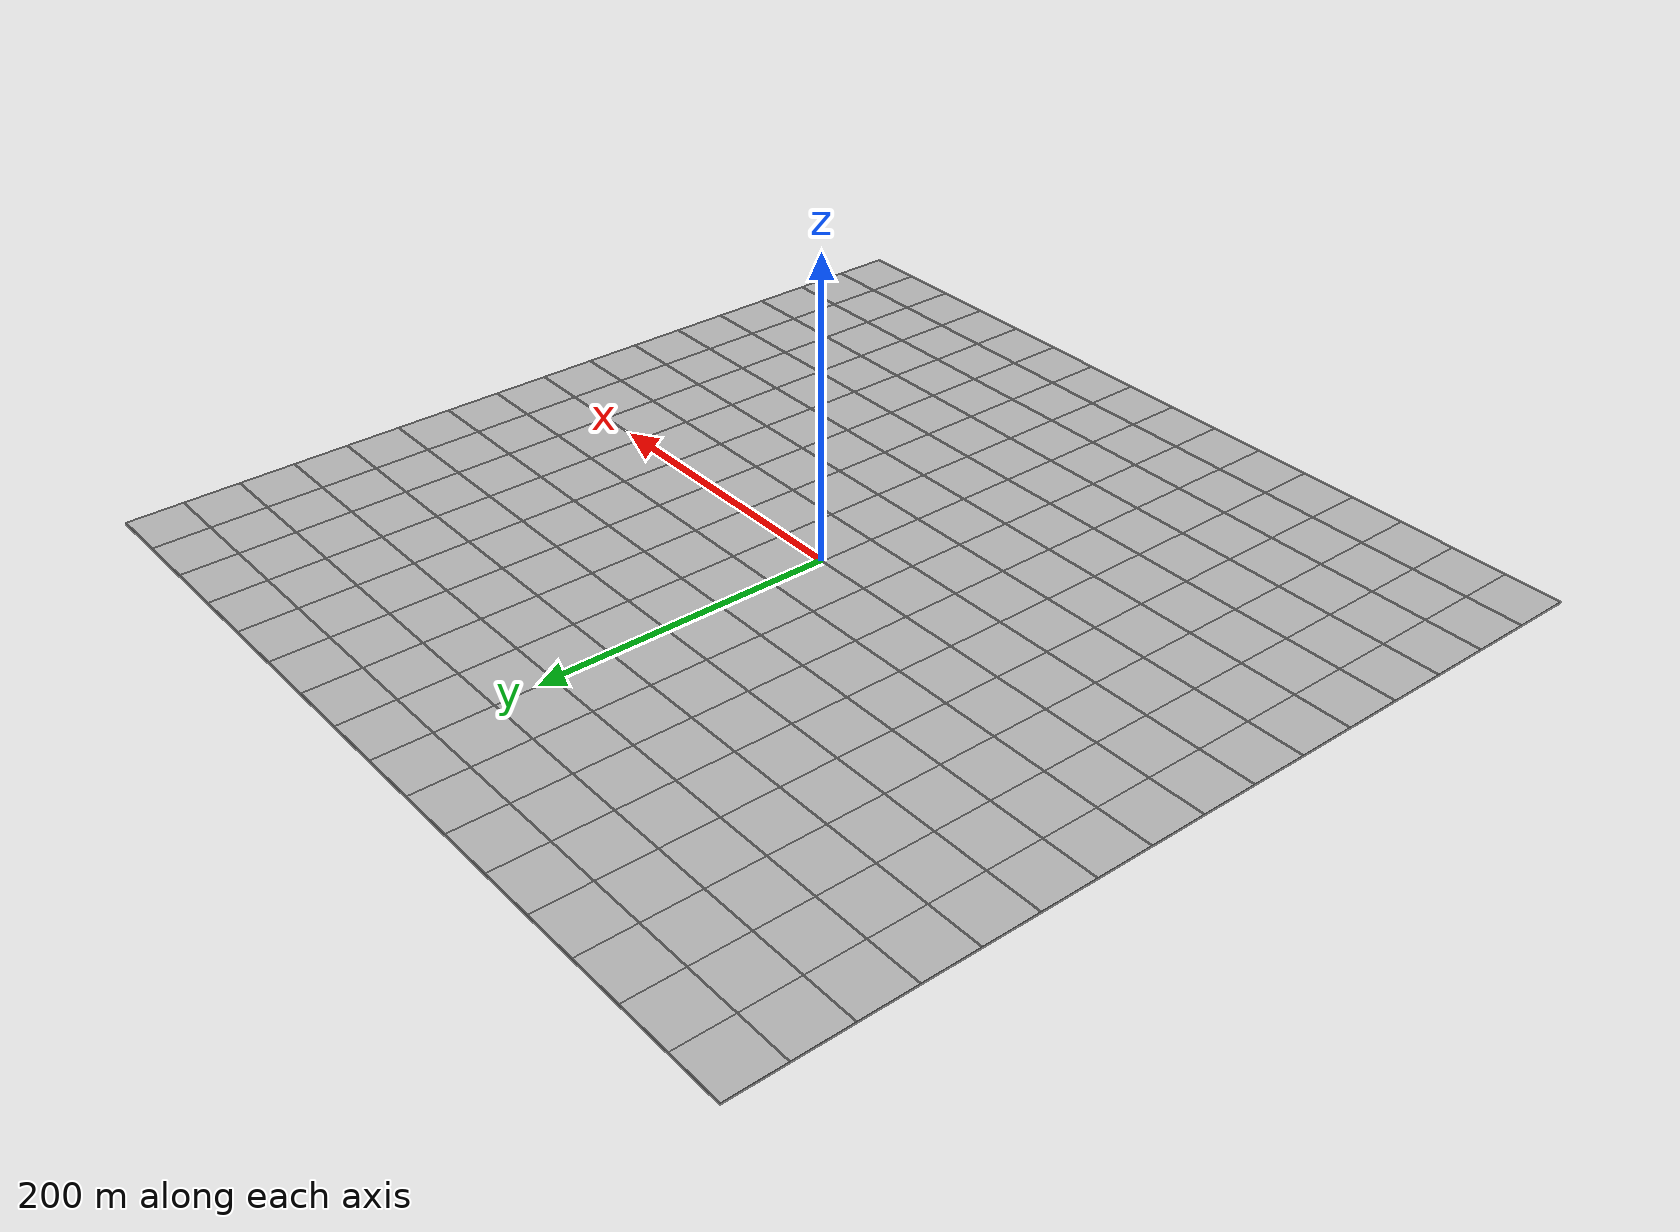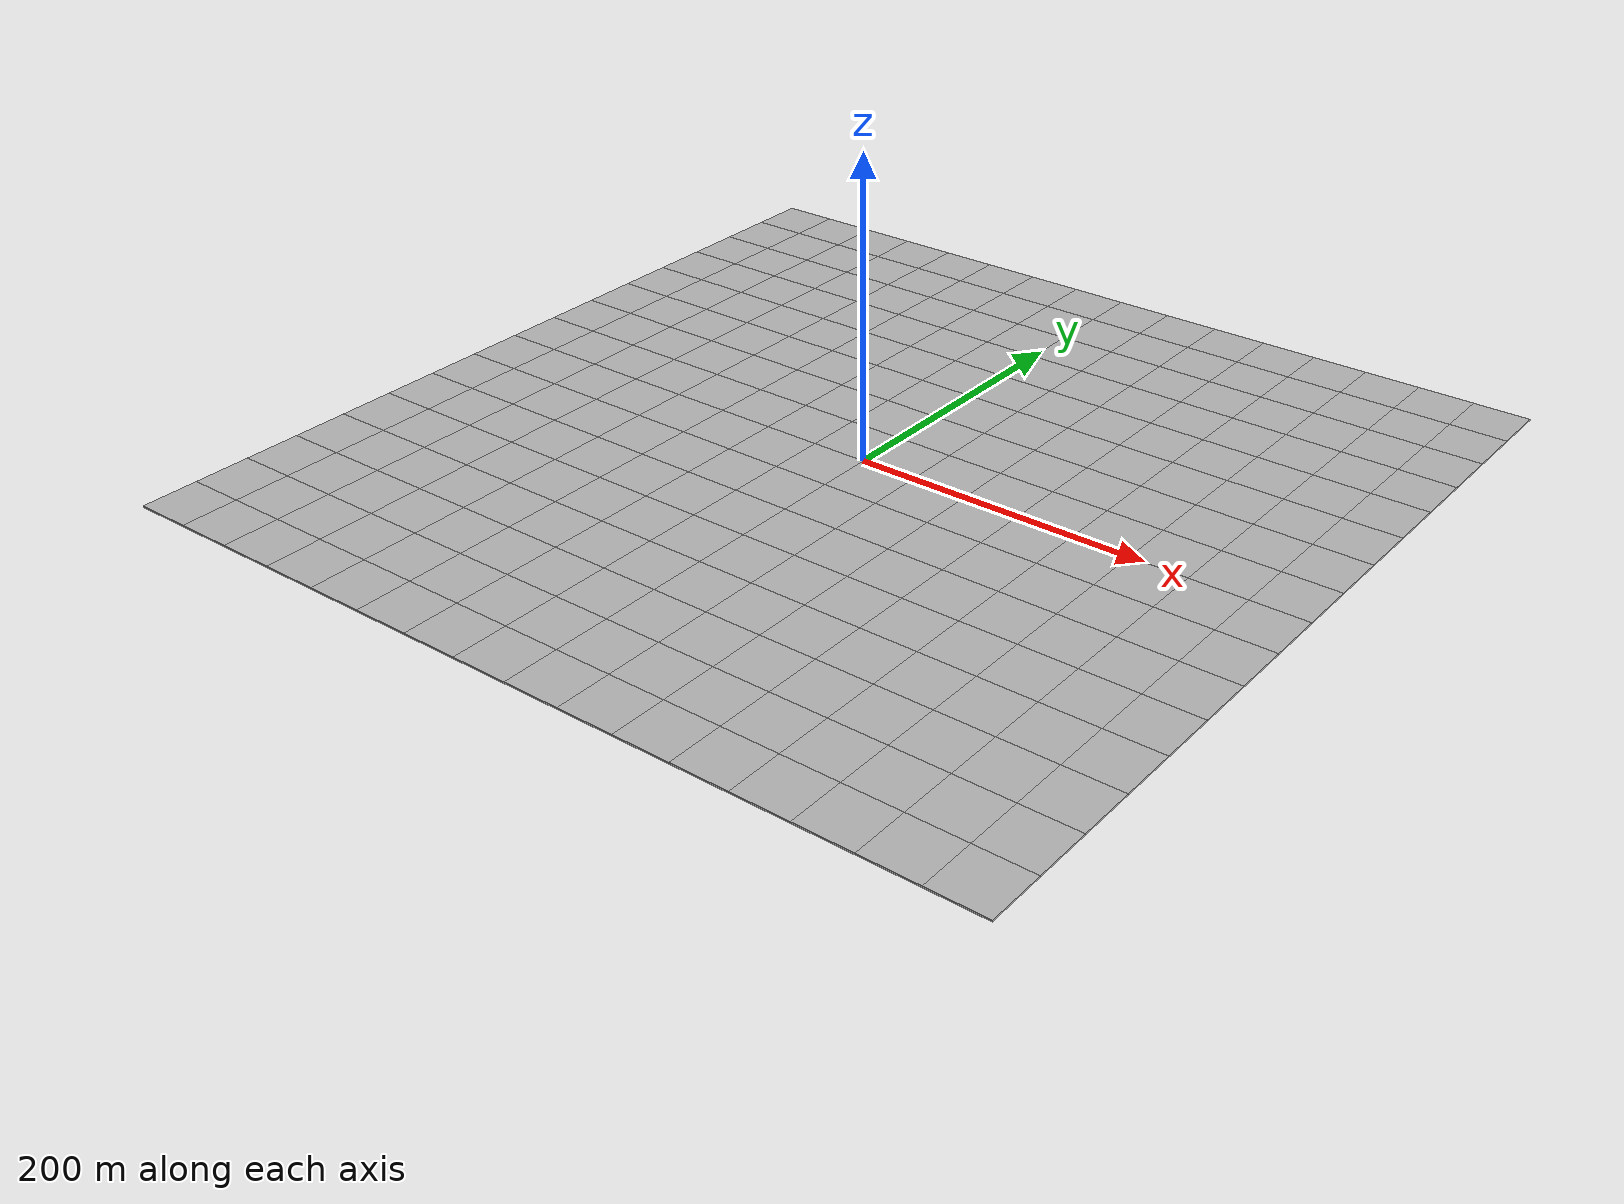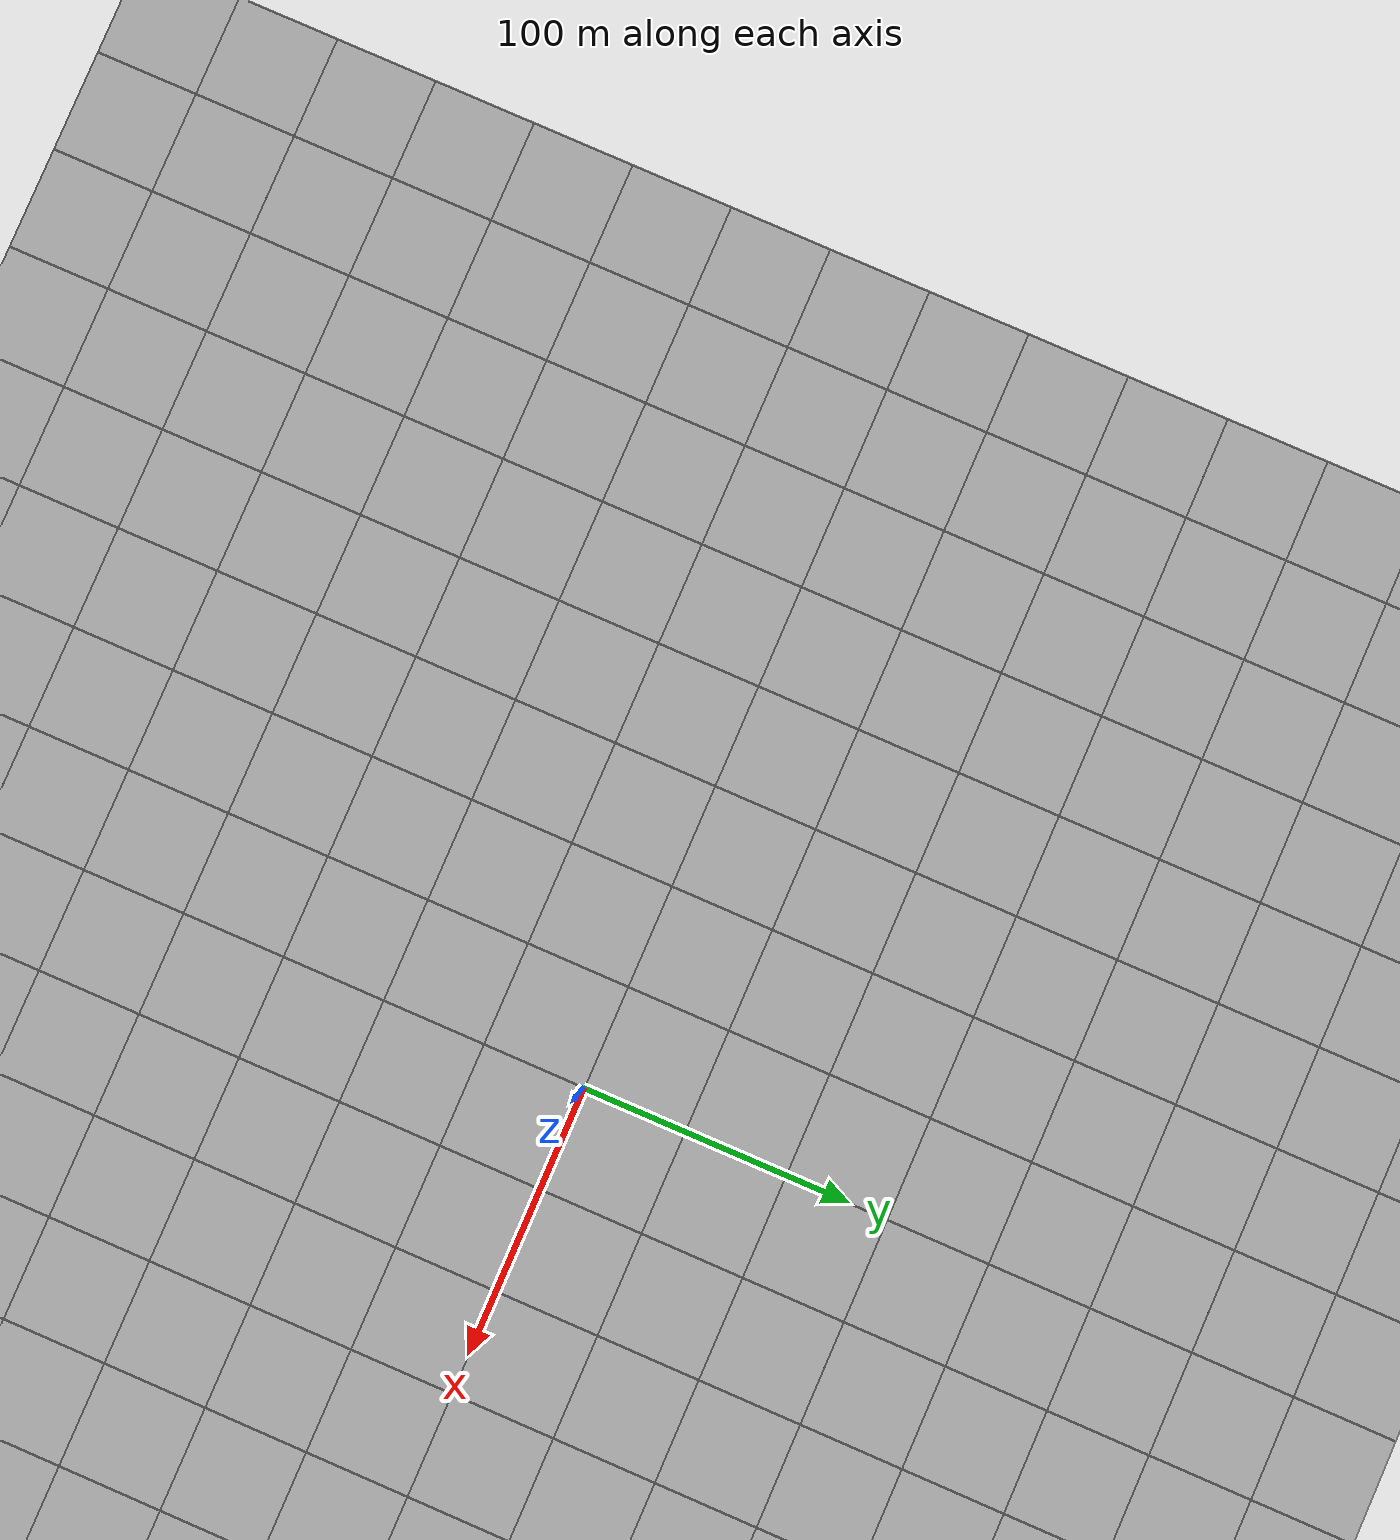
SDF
<sdf version="1.6">
 <world name="default">
  <light name="sun" type="directional">
   <pose>0 0 10 0 -0 0</pose>
   <diffuse>0.8 0.8 0.8 1</diffuse>
   <specular>0.2 0.2 0.2 1</specular>
   <attenuation>
    <range>1000</range>
    <constant>0.9</constant>
    <linear>0.01</linear>
    <quadratic>0.001</quadratic>
   </attenuation>
   <direction>-0.5 0.1 -0.9</direction>
  </light>
  <gravity>0 0 -9.8</gravity>
  <magnetic_field>6e-06 2.3e-05 -4.2e-05</magnetic_field>
  <atmosphere type="adiabatic"/>
  <physics name="default_physics" default="0" type="ode">
   <max_step_size>0.001</max_step_size>
   <real_time_factor>1</real_time_factor>
   <real_time_update_rate>1000</real_time_update_rate>
  </physics>
  <scene><ambient>1 1 1 1</ambient><background>0.7 0.7 0.7 1</background><shadows>1</shadows></scene>
  <audio><device>default</device></audio>
  <spherical_coordinates>
   <surface_model>EARTH_WGS84</surface_model>
   <latitude_deg>0</latitude_deg>
   <longitude_deg>0</longitude_deg>
   <elevation>0</elevation>
   <heading_deg>0</heading_deg>
  </spherical_coordinates>
  <plugin name="map" filename="libStaticMapPlugin.so">
   <center>37.228369 -80.423045</center>
   <world_size>600</world_size>
   <tile_size>640</tile_size>
   <map_type>satellite</map_type>
   <api_key>AIzaSyBa5-Ex915Um9s6yMzhjq10vkm2eksWVLc</api_key>
   <use_cache>1</use_cache>
  </plugin>
  <model name="map_satellite_37.228369_-80.423045_600_600">
   <static>1</static>
   <link name="link">
    <collision name="collision">
     <pose>0 0 -0.5 0 -0 0</pose>
     <geometry><box><size>608.615 608.615 1</size></box></geometry>
    </collision>
    <visual name="visual0_0">
     <pose>-285.288 285.288 -0.5 0 -0 1.5708</pose>
     <geometry><box><size>38.0384 38.0384 1</size></box></geometry>
     <material>
      <script>
       <uri>model://map_satellite_37.228369_-80.423045_600_600/materials/scripts</uri>
       <uri>model://map_satellite_37.228369_-80.423045_600_600/materials/textures</uri>
       <name>map_satellite_37.228369_-80.423045_600_600/0_0</name>
      </script>
     </material>
    </visual>
    <visual name="visual0_1">
     <pose>-247.25 285.288 -0.5 0 -0 1.5708</pose>
     <geometry><box><size>38.0384 38.0384 1</size></box></geometry>
     <material>
      <script>
       <uri>model://map_satellite_37.228369_-80.423045_600_600/materials/scripts</uri>
       <uri>model://map_satellite_37.228369_-80.423045_600_600/materials/textures</uri>
       <name>map_satellite_37.228369_-80.423045_600_600/0_1</name>
      </script>
     </material>
    </visual>
    <visual name="visual0_2">
     <pose>-209.211 285.288 -0.5 0 -0 1.5708</pose>
     <geometry><box><size>38.0384 38.0384 1</size></box></geometry>
     <material>
      <script>
       <uri>model://map_satellite_37.228369_-80.423045_600_600/materials/scripts</uri>
       <uri>model://map_satellite_37.228369_-80.423045_600_600/materials/textures</uri>
       <name>map_satellite_37.228369_-80.423045_600_600/0_2</name>
      </script>
     </material>
    </visual>
    <visual name="visual0_3">
     <pose>-171.173 285.288 -0.5 0 -0 1.5708</pose>
     <geometry><box><size>38.0384 38.0384 1</size></box></geometry>
     <material>
      <script>
       <uri>model://map_satellite_37.228369_-80.423045_600_600/materials/scripts</uri>
       <uri>model://map_satellite_37.228369_-80.423045_600_600/materials/textures</uri>
       <name>map_satellite_37.228369_-80.423045_600_600/0_3</name>
      </script>
     </material>
    </visual>
    <visual name="visual0_4">
     <pose>-133.135 285.288 -0.5 0 -0 1.5708</pose>
     <geometry><box><size>38.0384 38.0384 1</size></box></geometry>
     <material>
      <script>
       <uri>model://map_satellite_37.228369_-80.423045_600_600/materials/scripts</uri>
       <uri>model://map_satellite_37.228369_-80.423045_600_600/materials/textures</uri>
       <name>map_satellite_37.228369_-80.423045_600_600/0_4</name>
      </script>
     </material>
    </visual>
    <visual name="visual0_5">
     <pose>-95.0961 285.288 -0.5 0 -0 1.5708</pose>
     <geometry><box><size>38.0384 38.0384 1</size></box></geometry>
     <material>
      <script>
       <uri>model://map_satellite_37.228369_-80.423045_600_600/materials/scripts</uri>
       <uri>model://map_satellite_37.228369_-80.423045_600_600/materials/textures</uri>
       <name>map_satellite_37.228369_-80.423045_600_600/0_5</name>
      </script>
     </material>
    </visual>
    <visual name="visual0_6">
     <pose>-57.0576 285.288 -0.5 0 -0 1.5708</pose>
     <geometry><box><size>38.0384 38.0384 1</size></box></geometry>
     <material>
      <script>
       <uri>model://map_satellite_37.228369_-80.423045_600_600/materials/scripts</uri>
       <uri>model://map_satellite_37.228369_-80.423045_600_600/materials/textures</uri>
       <name>map_satellite_37.228369_-80.423045_600_600/0_6</name>
      </script>
     </material>
    </visual>
    <visual name="visual0_7">
     <pose>-19.0192 285.288 -0.5 0 -0 1.5708</pose>
     <geometry><box><size>38.0384 38.0384 1</size></box></geometry>
     <material>
      <script>
       <uri>model://map_satellite_37.228369_-80.423045_600_600/materials/scripts</uri>
       <uri>model://map_satellite_37.228369_-80.423045_600_600/materials/textures</uri>
       <name>map_satellite_37.228369_-80.423045_600_600/0_7</name>
      </script>
     </material>
    </visual>
    <visual name="visual0_8">
     <pose>19.0192 285.288 -0.5 0 -0 1.5708</pose>
     <geometry><box><size>38.0384 38.0384 1</size></box></geometry>
     <material>
      <script>
       <uri>model://map_satellite_37.228369_-80.423045_600_600/materials/scripts</uri>
       <uri>model://map_satellite_37.228369_-80.423045_600_600/materials/textures</uri>
       <name>map_satellite_37.228369_-80.423045_600_600/0_8</name>
      </script>
     </material>
    </visual>
    <visual name="visual0_9">
     <pose>57.0576 285.288 -0.5 0 -0 1.5708</pose>
     <geometry><box><size>38.0384 38.0384 1</size></box></geometry>
     <material>
      <script>
       <uri>model://map_satellite_37.228369_-80.423045_600_600/materials/scripts</uri>
       <uri>model://map_satellite_37.228369_-80.423045_600_600/materials/textures</uri>
       <name>map_satellite_37.228369_-80.423045_600_600/0_9</name>
      </script>
     </material>
    </visual>
    <visual name="visual0_10">
     <pose>95.0961 285.288 -0.5 0 -0 1.5708</pose>
     <geometry><box><size>38.0384 38.0384 1</size></box></geometry>
     <material>
      <script>
       <uri>model://map_satellite_37.228369_-80.423045_600_600/materials/scripts</uri>
       <uri>model://map_satellite_37.228369_-80.423045_600_600/materials/textures</uri>
       <name>map_satellite_37.228369_-80.423045_600_600/0_10</name>
      </script>
     </material>
    </visual>
    <visual name="visual0_11">
     <pose>133.135 285.288 -0.5 0 -0 1.5708</pose>
     <geometry><box><size>38.0384 38.0384 1</size></box></geometry>
     <material>
      <script>
       <uri>model://map_satellite_37.228369_-80.423045_600_600/materials/scripts</uri>
       <uri>model://map_satellite_37.228369_-80.423045_600_600/materials/textures</uri>
       <name>map_satellite_37.228369_-80.423045_600_600/0_11</name>
      </script>
     </material>
    </visual>
    <visual name="visual0_12">
     <pose>171.173 285.288 -0.5 0 -0 1.5708</pose>
     <geometry><box><size>38.0384 38.0384 1</size></box></geometry>
     <material>
      <script>
       <uri>model://map_satellite_37.228369_-80.423045_600_600/materials/scripts</uri>
       <uri>model://map_satellite_37.228369_-80.423045_600_600/materials/textures</uri>
       <name>map_satellite_37.228369_-80.423045_600_600/0_12</name>
      </script>
     </material>
    </visual>
    <visual name="visual0_13">
     <pose>209.211 285.288 -0.5 0 -0 1.5708</pose>
     <geometry><box><size>38.0384 38.0384 1</size></box></geometry>
     <material>
      <script>
       <uri>model://map_satellite_37.228369_-80.423045_600_600/materials/scripts</uri>
       <uri>model://map_satellite_37.228369_-80.423045_600_600/materials/textures</uri>
       <name>map_satellite_37.228369_-80.423045_600_600/0_13</name>
      </script>
     </material>
    </visual>
    <visual name="visual0_14">
     <pose>247.25 285.288 -0.5 0 -0 1.5708</pose>
     <geometry><box><size>38.0384 38.0384 1</size></box></geometry>
     <material>
      <script>
       <uri>model://map_satellite_37.228369_-80.423045_600_600/materials/scripts</uri>
       <uri>model://map_satellite_37.228369_-80.423045_600_600/materials/textures</uri>
       <name>map_satellite_37.228369_-80.423045_600_600/0_14</name>
      </script>
     </material>
    </visual>
    <visual name="visual0_15">
     <pose>285.288 285.288 -0.5 0 -0 1.5708</pose>
     <geometry><box><size>38.0384 38.0384 1</size></box></geometry>
     <material>
      <script>
       <uri>model://map_satellite_37.228369_-80.423045_600_600/materials/scripts</uri>
       <uri>model://map_satellite_37.228369_-80.423045_600_600/materials/textures</uri>
       <name>map_satellite_37.228369_-80.423045_600_600/0_15</name>
      </script>
     </material>
    </visual>
    <visual name="visual1_0">
     <pose>-285.288 247.25 -0.5 0 -0 1.5708</pose>
     <geometry><box><size>38.0384 38.0384 1</size></box></geometry>
     <material>
      <script>
       <uri>model://map_satellite_37.228369_-80.423045_600_600/materials/scripts</uri>
       <uri>model://map_satellite_37.228369_-80.423045_600_600/materials/textures</uri>
       <name>map_satellite_37.228369_-80.423045_600_600/1_0</name>
      </script>
     </material>
    </visual>
    <visual name="visual1_1">
     <pose>-247.25 247.25 -0.5 0 -0 1.5708</pose>
     <geometry><box><size>38.0384 38.0384 1</size></box></geometry>
     <material>
      <script>
       <uri>model://map_satellite_37.228369_-80.423045_600_600/materials/scripts</uri>
       <uri>model://map_satellite_37.228369_-80.423045_600_600/materials/textures</uri>
       <name>map_satellite_37.228369_-80.423045_600_600/1_1</name>
      </script>
     </material>
    </visual>
    <visual name="visual1_2">
     <pose>-209.211 247.25 -0.5 0 -0 1.5708</pose>
     <geometry><box><size>38.0384 38.0384 1</size></box></geometry>
     <material>
      <script>
       <uri>model://map_satellite_37.228369_-80.423045_600_600/materials/scripts</uri>
       <uri>model://map_satellite_37.228369_-80.423045_600_600/materials/textures</uri>
       <name>map_satellite_37.228369_-80.423045_600_600/1_2</name>
      </script>
     </material>
    </visual>
    <visual name="visual1_3">
     <pose>-171.173 247.25 -0.5 0 -0 1.5708</pose>
     <geometry><box><size>38.0384 38.0384 1</size></box></geometry>
     <material>
      <script>
       <uri>model://map_satellite_37.228369_-80.423045_600_600/materials/scripts</uri>
       <uri>model://map_satellite_37.228369_-80.423045_600_600/materials/textures</uri>
       <name>map_satellite_37.228369_-80.423045_600_600/1_3</name>
      </script>
     </material>
    </visual>
    <visual name="visual1_4">
     <pose>-133.135 247.25 -0.5 0 -0 1.5708</pose>
     <geometry><box><size>38.0384 38.0384 1</size></box></geometry>
     <material>
      <script>
       <uri>model://map_satellite_37.228369_-80.423045_600_600/materials/scripts</uri>
       <uri>model://map_satellite_37.228369_-80.423045_600_600/materials/textures</uri>
       <name>map_satellite_37.228369_-80.423045_600_600/1_4</name>
      </script>
     </material>
    </visual>
    <visual name="visual1_5">
     <pose>-95.0961 247.25 -0.5 0 -0 1.5708</pose>
     <geometry><box><size>38.0384 38.0384 1</size></box></geometry>
     <material>
      <script>
       <uri>model://map_satellite_37.228369_-80.423045_600_600/materials/scripts</uri>
       <uri>model://map_satellite_37.228369_-80.423045_600_600/materials/textures</uri>
       <name>map_satellite_37.228369_-80.423045_600_600/1_5</name>
      </script>
     </material>
    </visual>
    <visual name="visual1_6">
     <pose>-57.0576 247.25 -0.5 0 -0 1.5708</pose>
     <geometry><box><size>38.0384 38.0384 1</size></box></geometry>
     <material>
      <script>
       <uri>model://map_satellite_37.228369_-80.423045_600_600/materials/scripts</uri>
       <uri>model://map_satellite_37.228369_-80.423045_600_600/materials/textures</uri>
       <name>map_satellite_37.228369_-80.423045_600_600/1_6</name>
      </script>
     </material>
    </visual>
    <visual name="visual1_7">
     <pose>-19.0192 247.25 -0.5 0 -0 1.5708</pose>
     <geometry><box><size>38.0384 38.0384 1</size></box></geometry>
     <material>
      <script>
       <uri>model://map_satellite_37.228369_-80.423045_600_600/materials/scripts</uri>
       <uri>model://map_satellite_37.228369_-80.423045_600_600/materials/textures</uri>
       <name>map_satellite_37.228369_-80.423045_600_600/1_7</name>
      </script>
     </material>
    </visual>
    <visual name="visual1_8">
     <pose>19.0192 247.25 -0.5 0 -0 1.5708</pose>
     <geometry><box><size>38.0384 38.0384 1</size></box></geometry>
     <material>
      <script>
       <uri>model://map_satellite_37.228369_-80.423045_600_600/materials/scripts</uri>
       <uri>model://map_satellite_37.228369_-80.423045_600_600/materials/textures</uri>
       <name>map_satellite_37.228369_-80.423045_600_600/1_8</name>
      </script>
     </material>
    </visual>
    <visual name="visual1_9">
     <pose>57.0576 247.25 -0.5 0 -0 1.5708</pose>
     <geometry><box><size>38.0384 38.0384 1</size></box></geometry>
     <material>
      <script>
       <uri>model://map_satellite_37.228369_-80.423045_600_600/materials/scripts</uri>
       <uri>model://map_satellite_37.228369_-80.423045_600_600/materials/textures</uri>
       <name>map_satellite_37.228369_-80.423045_600_600/1_9</name>
      </script>
     </material>
    </visual>
    <visual name="visual1_10">
     <pose>95.0961 247.25 -0.5 0 -0 1.5708</pose>
     <geometry><box><size>38.0384 38.0384 1</size></box></geometry>
     <material>
      <script>
       <uri>model://map_satellite_37.228369_-80.423045_600_600/materials/scripts</uri>
       <uri>model://map_satellite_37.228369_-80.423045_600_600/materials/textures</uri>
       <name>map_satellite_37.228369_-80.423045_600_600/1_10</name>
      </script>
     </material>
    </visual>
    <visual name="visual1_11">
     <pose>133.135 247.25 -0.5 0 -0 1.5708</pose>
     <geometry><box><size>38.0384 38.0384 1</size></box></geometry>
     <material>
      <script>
       <uri>model://map_satellite_37.228369_-80.423045_600_600/materials/scripts</uri>
       <uri>model://map_satellite_37.228369_-80.423045_600_600/materials/textures</uri>
       <name>map_satellite_37.228369_-80.423045_600_600/1_11</name>
      </script>
     </material>
    </visual>
    <visual name="visual1_12">
     <pose>171.173 247.25 -0.5 0 -0 1.5708</pose>
     <geometry><box><size>38.0384 38.0384 1</size></box></geometry>
     <material>
      <script>
       <uri>model://map_satellite_37.228369_-80.423045_600_600/materials/scripts</uri>
       <uri>model://map_satellite_37.228369_-80.423045_600_600/materials/textures</uri>
       <name>map_satellite_37.228369_-80.423045_600_600/1_12</name>
      </script>
     </material>
    </visual>
    <visual name="visual1_13">
     <pose>209.211 247.25 -0.5 0 -0 1.5708</pose>
     <geometry><box><size>38.0384 38.0384 1</size></box></geometry>
     <material>
      <script>
       <uri>model://map_satellite_37.228369_-80.423045_600_600/materials/scripts</uri>
       <uri>model://map_satellite_37.228369_-80.423045_600_600/materials/textures</uri>
       <name>map_satellite_37.228369_-80.423045_600_600/1_13</name>
      </script>
     </material>
    </visual>
    <visual name="visual1_14">
     <pose>247.25 247.25 -0.5 0 -0 1.5708</pose>
     <geometry><box><size>38.0384 38.0384 1</size></box></geometry>
     <material>
      <script>
       <uri>model://map_satellite_37.228369_-80.423045_600_600/materials/scripts</uri>
       <uri>model://map_satellite_37.228369_-80.423045_600_600/materials/textures</uri>
       <name>map_satellite_37.228369_-80.423045_600_600/1_14</name>
      </script>
     </material>
    </visual>
    <visual name="visual1_15">
     <pose>285.288 247.25 -0.5 0 -0 1.5708</pose>
     <geometry><box><size>38.0384 38.0384 1</size></box></geometry>
     <material>
      <script>
       <uri>model://map_satellite_37.228369_-80.423045_600_600/materials/scripts</uri>
       <uri>model://map_satellite_37.228369_-80.423045_600_600/materials/textures</uri>
       <name>map_satellite_37.228369_-80.423045_600_600/1_15</name>
      </script>
     </material>
    </visual>
    <visual name="visual2_0">
     <pose>-285.288 209.211 -0.5 0 -0 1.5708</pose>
     <geometry><box><size>38.0384 38.0384 1</size></box></geometry>
     <material>
      <script>
       <uri>model://map_satellite_37.228369_-80.423045_600_600/materials/scripts</uri>
       <uri>model://map_satellite_37.228369_-80.423045_600_600/materials/textures</uri>
       <name>map_satellite_37.228369_-80.423045_600_600/2_0</name>
      </script>
     </material>
    </visual>
    <visual name="visual2_1">
     <pose>-247.25 209.211 -0.5 0 -0 1.5708</pose>
     <geometry><box><size>38.0384 38.0384 1</size></box></geometry>
     <material>
      <script>
       <uri>model://map_satellite_37.228369_-80.423045_600_600/materials/scripts</uri>
       <uri>model://map_satellite_37.228369_-80.423045_600_600/materials/textures</uri>
       <name>map_satellite_37.228369_-80.423045_600_600/2_1</name>
      </script>
     </material>
    </visual>
    <visual name="visual2_2">
     <pose>-209.211 209.211 -0.5 0 -0 1.5708</pose>
     <geometry><box><size>38.0384 38.0384 1</size></box></geometry>
     <material>
      <script>
       <uri>model://map_satellite_37.228369_-80.423045_600_600/materials/scripts</uri>
       <uri>model://map_satellite_37.228369_-80.423045_600_600/materials/textures</uri>
       <name>map_satellite_37.228369_-80.423045_600_600/2_2</name>
      </script>
     </material>
    </visual>
    <visual name="visual2_3">
     <pose>-171.173 209.211 -0.5 0 -0 1.5708</pose>
     <geometry><box><size>38.0384 38.0384 1</size></box></geometry>
     <material>
      <script>
       <uri>model://map_satellite_37.228369_-80.423045_600_600/materials/scripts</uri>
       <uri>model://map_satellite_37.228369_-80.423045_600_600/materials/textures</uri>
       <name>map_satellite_37.228369_-80.423045_600_600/2_3</name>
      </script>
     </material>
    </visual>
    <visual name="visual2_4">
     <pose>-133.135 209.211 -0.5 0 -0 1.5708</pose>
     <geometry><box><size>38.0384 38.0384 1</size></box></geometry>
     <material>
      <script>
       <uri>model://map_satellite_37.228369_-80.423045_600_600/materials/scripts</uri>
       <uri>model://map_satellite_37.228369_-80.423045_600_600/materials/textures</uri>
       <name>map_satellite_37.228369_-80.423045_600_600/2_4</name>
      </script>
     </material>
    </visual>
    <visual name="visual2_5">
     <pose>-95.0961 209.211 -0.5 0 -0 1.5708</pose>
     <geometry><box><size>38.0384 38.0384 1</size></box></geometry>
     <material>
      <script>
       <uri>model://map_satellite_37.228369_-80.423045_600_600/materials/scripts</uri>
       <uri>model://map_satellite_37.228369_-80.423045_600_600/materials/textures</uri>
       <name>map_satellite_37.228369_-80.423045_600_600/2_5</name>
      </script>
     </material>
    </visual>
    <visual name="visual2_6">
     <pose>-57.0576 209.211 -0.5 0 -0 1.5708</pose>
     <geometry><box><size>38.0384 38.0384 1</size></box></geometry>
     <material>
      <script>
       <uri>model://map_satellite_37.228369_-80.423045_600_600/materials/scripts</uri>
       <uri>model://map_satellite_37.228369_-80.423045_600_600/materials/textures</uri>
       <name>map_satellite_37.228369_-80.423045_600_600/2_6</name>
      </script>
     </material>
    </visual>
    <visual name="visual2_7">
     <pose>-19.0192 209.211 -0.5 0 -0 1.5708</pose>
     <geometry><box><size>38.0384 38.0384 1</size></box></geometry>
     <material>
      <script>
       <uri>model://map_satellite_37.228369_-80.423045_600_600/materials/scripts</uri>
       <uri>model://map_satellite_37.228369_-80.423045_600_600/materials/textures</uri>
       <name>map_satellite_37.228369_-80.423045_600_600/2_7</name>
      </script>
     </material>
    </visual>
    <visual name="visual2_8">
     <pose>19.0192 209.211 -0.5 0 -0 1.5708</pose>
     <geometry><box><size>38.0384 38.0384 1</size></box></geometry>
     <material>
      <script>
       <uri>model://map_satellite_37.228369_-80.423045_600_600/materials/scripts</uri>
       <uri>model://map_satellite_37.228369_-80.423045_600_600/materials/textures</uri>
       <name>map_satellite_37.228369_-80.423045_600_600/2_8</name>
      </script>
     </material>
    </visual>
    <visual name="visual2_9">
     <pose>57.0576 209.211 -0.5 0 -0 1.5708</pose>
     <geometry><box><size>38.0384 38.0384 1</size></box></geometry>
     <material>
      <script>
       <uri>model://map_satellite_37.228369_-80.423045_600_600/materials/scripts</uri>
       <uri>model://map_satellite_37.228369_-80.423045_600_600/materials/textures</uri>
       <name>map_satellite_37.228369_-80.423045_600_600/2_9</name>
      </script>
     </material>
    </visual>
    <visual name="visual2_10">
     <pose>95.0961 209.211 -0.5 0 -0 1.5708</pose>
     <geometry><box><size>38.0384 38.0384 1</size></box></geometry>
     <material>
      <script>
       <uri>model://map_satellite_37.228369_-80.423045_600_600/materials/scripts</uri>
       <uri>model://map_satellite_37.228369_-80.423045_600_600/materials/textures</uri>
       <name>map_satellite_37.228369_-80.423045_600_600/2_10</name>
      </script>
     </material>
    </visual>
    <visual name="visual2_11">
     <pose>133.135 209.211 -0.5 0 -0 1.5708</pose>
     <geometry><box><size>38.0384 38.0384 1</size></box></geometry>
     <material>
      <script>
       <uri>model://map_satellite_37.228369_-80.423045_600_600/materials/scripts</uri>
       <uri>model://map_satellite_37.228369_-80.423045_600_600/materials/textures</uri>
       <name>map_satellite_37.228369_-80.423045_600_600/2_11</name>
      </script>
     </material>
    </visual>
    <visual name="visual2_12">
     <pose>171.173 209.211 -0.5 0 -0 1.5708</pose>
     <geometry><box><size>38.0384 38.0384 1</size></box></geometry>
     <material>
      <script>
       <uri>model://map_satellite_37.228369_-80.423045_600_600/materials/scripts</uri>
       <uri>model://map_satellite_37.228369_-80.423045_600_600/materials/textures</uri>
       <name>map_satellite_37.228369_-80.423045_600_600/2_12</name>
      </script>
     </material>
    </visual>
    <visual name="visual2_13">
     <pose>209.211 209.211 -0.5 0 -0 1.5708</pose>
     <geometry><box><size>38.0384 38.0384 1</size></box></geometry>
     <material>
      <script>
       <uri>model://map_satellite_37.228369_-80.423045_600_600/materials/scripts</uri>
       <uri>model://map_satellite_37.228369_-80.423045_600_600/materials/textures</uri>
       <name>map_satellite_37.228369_-80.423045_600_600/2_13</name>
      </script>
     </material>
    </visual>
    <visual name="visual2_14">
     <pose>247.25 209.211 -0.5 0 -0 1.5708</pose>
     <geometry><box><size>38.0384 38.0384 1</size></box></geometry>
     <material>
      <script>
       <uri>model://map_satellite_37.228369_-80.423045_600_600/materials/scripts</uri>
       <uri>model://map_satellite_37.228369_-80.423045_600_600/materials/textures</uri>
       <name>map_satellite_37.228369_-80.423045_600_600/2_14</name>
      </script>
     </material>
    </visual>
    <visual name="visual2_15">
     <pose>285.288 209.211 -0.5 0 -0 1.5708</pose>
     <geometry><box><size>38.0384 38.0384 1</size></box></geometry>
     <material>
      <script>
       <uri>model://map_satellite_37.228369_-80.423045_600_600/materials/scripts</uri>
       <uri>model://map_satellite_37.228369_-80.423045_600_600/materials/textures</uri>
       <name>map_satellite_37.228369_-80.423045_600_600/2_15</name>
      </script>
     </material>
    </visual>
    <visual name="visual3_0">
     <pose>-285.288 171.173 -0.5 0 -0 1.5708</pose>
     <geometry><box><size>38.0384 38.0384 1</size></box></geometry>
     <material>
      <script>
       <uri>model://map_satellite_37.228369_-80.423045_600_600/materials/scripts</uri>
       <uri>model://map_satellite_37.228369_-80.423045_600_600/materials/textures</uri>
       <name>map_satellite_37.228369_-80.423045_600_600/3_0</name>
      </script>
     </material>
    </visual>
    <visual name="visual3_1">
     <pose>-247.25 171.173 -0.5 0 -0 1.5708</pose>
     <geometry><box><size>38.0384 38.0384 1</size></box></geometry>
     <material>
      <script>
       <uri>model://map_satellite_37.228369_-80.423045_600_600/materials/scripts</uri>
       <uri>model://map_satellite_37.228369_-80.423045_600_600/materials/textures</uri>
       <name>map_satellite_37.228369_-80.423045_600_600/3_1</name>
      </script>
     </material>
    </visual>
    <visual name="visual3_2">
     <pose>-209.211 171.173 -0.5 0 -0 1.5708</pose>
     <geometry><box><size>38.0384 38.0384 1</size></box></geometry>
     <material>
      <script>
       <uri>model://map_satellite_37.228369_-80.423045_600_600/materials/scripts</uri>
       <uri>model://map_satellite_37.228369_-80.423045_600_600/materials/textures</uri>
       <name>map_satellite_37.228369_-80.423045_600_600/3_2</name>
      </script>
     </material>
    </visual>
    <visual name="visual3_3">
     <pose>-171.173 171.173 -0.5 0 -0 1.5708</pose>
     <geometry><box><size>38.0384 38.0384 1</size></box></geometry>
     <material>
      <script>
       <uri>model://map_satellite_37.228369_-80.423045_600_600/materials/scripts</uri>
       <uri>model://map_satellite_37.228369_-80.423045_600_600/materials/textures</uri>
       <name>map_satellite_37.228369_-80.423045_600_600/3_3</name>
      </script>
     </material>
    </visual>
    <visual name="visual3_4">
     <pose>-133.135 171.173 -0.5 0 -0 1.5708</pose>
     <geometry><box><size>38.0384 38.0384 1</size></box></geometry>
     <material>
      <script>
       <uri>model://map_satellite_37.228369_-80.423045_600_600/materials/scripts</uri>
       <uri>model://map_satellite_37.228369_-80.423045_600_600/materials/textures</uri>
       <name>map_satellite_37.228369_-80.423045_600_600/3_4</name>
      </script>
     </material>
    </visual>
    <visual name="visual3_5">
     <pose>-95.0961 171.173 -0.5 0 -0 1.5708</pose>
     <geometry><box><size>38.0384 38.0384 1</size></box></geometry>
     <material>
      <script>
       <uri>model://map_satellite_37.228369_-80.423045_600_600/materials/scripts</uri>
       <uri>model://map_satellite_37.228369_-80.423045_600_600/materials/textures</uri>
       <name>map_satellite_37.228369_-80.423045_600_600/3_5</name>
      </script>
     </material>
    </visual>
    <visual name="visual3_6">
     <pose>-57.0576 171.173 -0.5 0 -0 1.5708</pose>
     <geometry><box><size>38.0384 38.0384 1</size></box></geometry>
     <material>
      <script>
       <uri>model://map_satellite_37.228369_-80.423045_600_600/materials/scripts</uri>
       <uri>model://map_satellite_37.228369_-80.423045_600_600/materials/textures</uri>
       <name>map_satellite_37.228369_-80.423045_600_600/3_6</name>
      </script>
     </material>
    </visual>
    <visual name="visual3_7">
     <pose>-19.0192 171.173 -0.5 0 -0 1.5708</pose>
     <geometry><box><size>38.0384 38.0384 1</size></box></geometry>
     <material>
      <script>
       <uri>model://map_satellite_37.228369_-80.423045_600_600/materials/scripts</uri>
       <uri>model://map_satellite_37.228369_-80.423045_600_600/materials/textures</uri>
       <name>map_satellite_37.228369_-80.423045_600_600/3_7</name>
      </script>
     </material>
    </visual>
    <visual name="visual3_8">
     <pose>19.0192 171.173 -0.5 0 -0 1.5708</pose>
     <geometry><box><size>38.0384 38.0384 1</size></box></geometry>
     <material>
      <script>
       <uri>model://map_satellite_37.228369_-80.423045_600_600/materials/scripts</uri>
       <uri>model://map_satellite_37.228369_-80.423045_600_600/materials/textures</uri>
       <name>map_satellite_37.228369_-80.423045_600_600/3_8</name>
      </script>
     </material>
    </visual>
    <visual name="visual3_9">
     <pose>57.0576 171.173 -0.5 0 -0 1.5708</pose>
     <geometry><box><size>38.0384 38.0384 1</size></box></geometry>
     <material>
      <script>
       <uri>model://map_satellite_37.228369_-80.423045_600_600/materials/scripts</uri>
       <uri>model://map_satellite_37.228369_-80.423045_600_600/materials/textures</uri>
       <name>map_satellite_37.228369_-80.423045_600_600/3_9</name>
      </script>
     </material>
    </visual>
    <visual name="visual3_10">
     <pose>95.0961 171.173 -0.5 0 -0 1.5708</pose>
     <geometry><box><size>38.0384 38.0384 1</size></box></geometry>
     <material>
      <script>
       <uri>model://map_satellite_37.228369_-80.423045_600_600/materials/scripts</uri>
       <uri>model://map_satellite_37.228369_-80.423045_600_600/materials/textures</uri>
       <name>map_satellite_37.228369_-80.423045_600_600/3_10</name>
      </script>
     </material>
    </visual>
    <visual name="visual3_11">
     <pose>133.135 171.173 -0.5 0 -0 1.5708</pose>
     <geometry><box><size>38.0384 38.0384 1</size></box></geometry>
     <material>
      <script>
       <uri>model://map_satellite_37.228369_-80.423045_600_600/materials/scripts</uri>
       <uri>model://map_satellite_37.228369_-80.423045_600_600/materials/textures</uri>
       <name>map_satellite_37.228369_-80.423045_600_600/3_11</name>
      </script>
     </material>
    </visual>
    <visual name="visual3_12">
     <pose>171.173 171.173 -0.5 0 -0 1.5708</pose>
     <geometry><box><size>38.0384 38.0384 1</size></box></geometry>
     <material>
      <script>
       <uri>model://map_satellite_37.228369_-80.423045_600_600/materials/scripts</uri>
       <uri>model://map_satellite_37.228369_-80.423045_600_600/materials/textures</uri>
       <name>map_satellite_37.228369_-80.423045_600_600/3_12</name>
      </script>
     </material>
    </visual>
    <visual name="visual3_13">
     <pose>209.211 171.173 -0.5 0 -0 1.5708</pose>
     <geometry><box><size>38.0384 38.0384 1</size></box></geometry>
     <material>
      <script>
       <uri>model://map_satellite_37.228369_-80.423045_600_600/materials/scripts</uri>
       <uri>model://map_satellite_37.228369_-80.423045_600_600/materials/textures</uri>
       <name>map_satellite_37.228369_-80.423045_600_600/3_13</name>
      </script>
     </material>
    </visual>
    <visual name="visual3_14">
     <pose>247.25 171.173 -0.5 0 -0 1.5708</pose>
     <geometry><box><size>38.0384 38.0384 1</size></box></geometry>
     <material>
      <script>
       <uri>model://map_satellite_37.228369_-80.423045_600_600/materials/scripts</uri>
       <uri>model://map_satellite_37.228369_-80.423045_600_600/materials/textures</uri>
       <name>map_satellite_37.228369_-80.423045_600_600/3_14</name>
      </script>
     </material>
    </visual>
    <visual name="visual3_15">
     <pose>285.288 171.173 -0.5 0 -0 1.5708</pose>
     <geometry><box><size>38.0384 38.0384 1</size></box></geometry>
     <material>
      <script>
       <uri>model://map_satellite_37.228369_-80.423045_600_600/materials/scripts</uri>
       <uri>model://map_satellite_37.228369_-80.423045_600_600/materials/textures</uri>
       <name>map_satellite_37.228369_-80.423045_600_600/3_15</name>
      </script>
     </material>
    </visual>
    <visual name="visual4_0">
     <pose>-285.288 133.135 -0.5 0 -0 1.5708</pose>
     <geometry><box><size>38.0384 38.0384 1</size></box></geometry>
     <material>
      <script>
       <uri>model://map_satellite_37.228369_-80.423045_600_600/materials/scripts</uri>
       <uri>model://map_satellite_37.228369_-80.423045_600_600/materials/textures</uri>
       <name>map_satellite_37.228369_-80.423045_600_600/4_0</name>
      </script>
     </material>
    </visual>
    <visual name="visual4_1">
     <pose>-247.25 133.135 -0.5 0 -0 1.5708</pose>
     <geometry><box><size>38.0384 38.0384 1</size></box></geometry>
     <material>
      <script>
       <uri>model://map_satellite_37.228369_-80.423045_600_600/materials/scripts</uri>
       <uri>model://map_satellite_37.228369_-80.423045_600_600/materials/textures</uri>
       <name>map_satellite_37.228369_-80.423045_600_600/4_1</name>
      </script>
     </material>
    </visual>
    <visual name="visual4_2">
     <pose>-209.211 133.135 -0.5 0 -0 1.5708</pose>
     <geometry><box><size>38.0384 38.0384 1</size></box></geometry>
     <material>
      <script>
       <uri>model://map_satellite_37.228369_-80.423045_600_600/materials/scripts</uri>
       <uri>model://map_satellite_37.228369_-80.423045_600_600/materials/textures</uri>
       <name>map_satellite_37.228369_-80.423045_600_600/4_2</name>
      </script>
     </material>
    </visual>
    <visual name="visual4_3">
     <pose>-171.173 133.135 -0.5 0 -0 1.5708</pose>
     <geometry><box><size>38.0384 38.0384 1</size></box></geometry>
     <material>
      <script>
       <uri>model://map_satellite_37.228369_-80.423045_600_600/materials/scripts</uri>
       <uri>model://map_satellite_37.228369_-80.423045_600_600/materials/textures</uri>
       <name>map_satellite_37.228369_-80.423045_600_600/4_3</name>
      </script>
     </material>
    </visual>
    <visual name="visual4_4">
     <pose>-133.135 133.135 -0.5 0 -0 1.5708</pose>
     <geometry><box><size>38.0384 38.0384 1</size></box></geometry>
     <material>
      <script>
       <uri>model://map_satellite_37.228369_-80.423045_600_600/materials/scripts</uri>
       <uri>model://map_satellite_37.228369_-80.423045_600_600/materials/textures</uri>
       <name>map_satellite_37.228369_-80.423045_600_600/4_4</name>
      </script>
     </material>
    </visual>
    <visual name="visual4_5">
     <pose>-95.0961 133.135 -0.5 0 -0 1.5708</pose>
     <geometry><box><size>38.0384 38.0384 1</size></box></geometry>
     <material>
      <script>
       <uri>model://map_satellite_37.228369_-80.423045_600_600/materials/scripts</uri>
       <uri>model://map_satellite_37.228369_-80.423045_600_600/materials/textures</uri>
       <name>map_satellite_37.228369_-80.423045_600_600/4_5</name>
      </script>
     </material>
    </visual>
    <visual name="visual4_6">
     <pose>-57.0576 133.135 -0.5 0 -0 1.5708</pose>
     <geometry><box><size>38.0384 38.0384 1</size></box></geometry>
     <material>
      <script>
       <uri>model://map_satellite_37.228369_-80.423045_600_600/materials/scripts</uri>
       <uri>model://map_satellite_37.228369_-80.423045_600_600/materials/textures</uri>
       <name>map_satellite_37.228369_-80.423045_600_600/4_6</name>
      </script>
     </material>
    </visual>
    <visual name="visual4_7">
     <pose>-19.0192 133.135 -0.5 0 -0 1.5708</pose>
     <geometry><box><size>38.0384 38.0384 1</size></box></geometry>
     <material>
      <script>
       <uri>model://map_satellite_37.228369_-80.423045_600_600/materials/scripts</uri>
       <uri>model://map_satellite_37.228369_-80.423045_600_600/materials/textures</uri>
       <name>map_satellite_37.228369_-80.423045_600_600/4_7</name>
      </script>
     </material>
    </visual>
    <visual name="visual4_8">
     <pose>19.0192 133.135 -0.5 0 -0 1.5708</pose>
     <geometry><box><size>38.0384 38.0384 1</size></box></geometry>
     <material>
      <script>
       <uri>model://map_satellite_37.228369_-80.423045_600_600/materials/scripts</uri>
       <uri>model://map_satellite_37.228369_-80.423045_600_600/materials/textures</uri>
       <name>map_satellite_37.228369_-80.423045_600_600/4_8</name>
      </script>
     </material>
    </visual>
    <visual name="visual4_9">
     <pose>57.0576 133.135 -0.5 0 -0 1.5708</pose>
     <geometry><box><size>38.0384 38.0384 1</size></box></geometry>
     <material>
      <script>
       <uri>model://map_satellite_37.228369_-80.423045_600_600/materials/scripts</uri>
       <uri>model://map_satellite_37.228369_-80.423045_600_600/materials/textures</uri>
       <name>map_satellite_37.228369_-80.423045_600_600/4_9</name>
      </script>
     </material>
    </visual>
    <visual name="visual4_10">
     <pose>95.0961 133.135 -0.5 0 -0 1.5708</pose>
     <geometry><box><size>38.0384 38.0384 1</size></box></geometry>
     <material>
      <script>
       <uri>model://map_satellite_37.228369_-80.423045_600_600/materials/scripts</uri>
       <uri>model://map_satellite_37.228369_-80.423045_600_600/materials/textures</uri>
       <name>map_satellite_37.228369_-80.423045_600_600/4_10</name>
      </script>
     </material>
    </visual>
    <visual name="visual4_11">
     <pose>133.135 133.135 -0.5 0 -0 1.5708</pose>
     <geometry><box><size>38.0384 38.0384 1</size></box></geometry>
     <material>
      <script>
       <uri>model://map_satellite_37.228369_-80.423045_600_600/materials/scripts</uri>
       <uri>model://map_satellite_37.228369_-80.423045_600_600/materials/textures</uri>
       <name>map_satellite_37.228369_-80.423045_600_600/4_11</name>
      </script>
     </material>
    </visual>
    <visual name="visual4_12">
     <pose>171.173 133.135 -0.5 0 -0 1.5708</pose>
     <geometry><box><size>38.0384 38.0384 1</size></box></geometry>
     <material>
      <script>
       <uri>model://map_satellite_37.228369_-80.423045_600_600/materials/scripts</uri>
       <uri>model://map_satellite_37.228369_-80.423045_600_600/materials/textures</uri>
       <name>map_satellite_37.228369_-80.423045_600_600/4_12</name>
      </script>
     </material>
    </visual>
    <visual name="visual4_13">
     <pose>209.211 133.135 -0.5 0 -0 1.5708</pose>
     <geometry><box><size>38.0384 38.0384 1</size></box></geometry>
     <material>
      <script>
       <uri>model://map_satellite_37.228369_-80.423045_600_600/materials/scripts</uri>
       <uri>model://map_satellite_37.228369_-80.423045_600_600/materials/textures</uri>
       <name>map_satellite_37.228369_-80.423045_600_600/4_13</name>
      </script>
     </material>
    </visual>
    <visual name="visual4_14">
     <pose>247.25 133.135 -0.5 0 -0 1.5708</pose>
     <geometry><box><size>38.0384 38.0384 1</size></box></geometry>
     <material>
      <script>
       <uri>model://map_satellite_37.228369_-80.423045_600_600/materials/scripts</uri>
       <uri>model://map_satellite_37.228369_-80.423045_600_600/materials/textures</uri>
       <name>map_satellite_37.228369_-80.423045_600_600/4_14</name>
      </script>
     </material>
    </visual>
    <visual name="visual4_15">
     <pose>285.288 133.135 -0.5 0 -0 1.5708</pose>
     <geometry><box><size>38.0384 38.0384 1</size></box></geometry>
     <material>
      <script>
       <uri>model://map_satellite_37.228369_-80.423045_600_600/materials/scripts</uri>
       <uri>model://map_satellite_37.228369_-80.423045_600_600/materials/textures</uri>
       <name>map_satellite_37.228369_-80.423045_600_600/4_15</name>
      </script>
     </material>
    </visual>
    <visual name="visual5_0">
     <pose>-285.288 95.0961 -0.5 0 -0 1.5708</pose>
     <geometry><box><size>38.0384 38.0384 1</size></box></geometry>
     <material>
      <script>
       <uri>model://map_satellite_37.228369_-80.423045_600_600/materials/scripts</uri>
       <uri>model://map_satellite_37.228369_-80.423045_600_600/materials/textures</uri>
       <name>map_satellite_37.228369_-80.423045_600_600/5_0</name>
      </script>
     </material>
    </visual>
    <visual name="visual5_1">
     <pose>-247.25 95.0961 -0.5 0 -0 1.5708</pose>
     <geometry><box><size>38.0384 38.0384 1</size></box></geometry>
     <material>
      <script>
       <uri>model://map_satellite_37.228369_-80.423045_600_600/materials/scripts</uri>
       <uri>model://map_satellite_37.228369_-80.423045_600_600/materials/textures</uri>
       <name>map_satellite_37.228369_-80.423045_600_600/5_1</name>
      </script>
     </material>
    </visual>
    <visual name="visual5_2">
     <pose>-209.211 95.0961 -0.5 0 -0 1.5708</pose>
     <geometry><box><size>38.0384 38.0384 1</size></box></geometry>
     <material>
      <script>
       <uri>model://map_satellite_37.228369_-80.423045_600_600/materials/scripts</uri>
       <uri>model://map_satellite_37.228369_-80.423045_600_600/materials/textures</uri>
       <name>map_satellite_37.228369_-80.423045_600_600/5_2</name>
      </script>
     </material>
    </visual>
    <visual name="visual5_3">
     <pose>-171.173 95.0961 -0.5 0 -0 1.5708</pose>
     <geometry><box><size>38.0384 38.0384 1</size></box></geometry>
     <material>
      <script>
       <uri>model://map_satellite_37.228369_-80.423045_600_600/materials/scripts</uri>
       <uri>model://map_satellite_37.228369_-80.423045_600_600/materials/textures</uri>
       <name>map_satellite_37.228369_-80.423045_600_600/5_3</name>
      </script>
     </material>
    </visual>
    <visual name="visual5_4">
     <pose>-133.135 95.0961 -0.5 0 -0 1.5708</pose>
     <geometry><box><size>38.0384 38.0384 1</size></box></geometry>
     <material>
      <script>
       <uri>model://map_satellite_37.228369_-80.423045_600_600/materials/scripts</uri>
       <uri>model://map_satellite_37.228369_-80.423045_600_600/materials/textures</uri>
       <name>map_satellite_37.228369_-80.423045_600_600/5_4</name>
      </script>
     </material>
    </visual>
    <visual name="visual5_5">
     <pose>-95.0961 95.0961 -0.5 0 -0 1.5708</pose>
     <geometry><box><size>38.0384 38.0384 1</size></box></geometry>
     <material>
      <script>
       <uri>model://map_satellite_37.228369_-80.423045_600_600/materials/scripts</uri>
       <uri>model://map_satellite_37.228369_-80.423045_600_600/materials/textures</uri>
       <name>map_satellite_37.228369_-80.423045_600_600/5_5</name>
      </script>
     </material>
    </visual>
    <visual name="visual5_6">
     <pose>-57.0576 95.0961 -0.5 0 -0 1.5708</pose>
     <geometry><box><size>38.0384 38.0384 1</size></box></geometry>
     <material>
      <script>
       <uri>model://map_satellite_37.228369_-80.423045_600_600/materials/scripts</uri>
       <uri>model://map_satellite_37.228369_-80.423045_600_600/materials/textures</uri>
       <name>map_satellite_37.228369_-80.423045_600_600/5_6</name>
      </script>
     </material>
    </visual>
    <visual name="visual5_7">
     <pose>-19.0192 95.0961 -0.5 0 -0 1.5708</pose>
     <geometry><box><size>38.0384 38.0384 1</size></box></geometry>
     <material>
      <script>
       <uri>model://map_satellite_37.228369_-80.423045_600_600/materials/scripts</uri>
       <uri>model://map_satellite_37.228369_-80.423045_600_600/materials/textures</uri>
       <name>map_satellite_37.228369_-80.423045_600_600/5_7</name>
      </script>
     </material>
    </visual>
    <visual name="visual5_8">
     <pose>19.0192 95.0961 -0.5 0 -0 1.5708</pose>
     <geometry><box><size>38.0384 38.0384 1</size></box></geometry>
     <material>
      <script>
       <uri>model://map_satellite_37.228369_-80.423045_600_600/materials/scripts</uri>
       <uri>model://map_satellite_37.228369_-80.423045_600_600/materials/textures</uri>
       <name>map_satellite_37.228369_-80.423045_600_600/5_8</name>
      </script>
     </material>
    </visual>
    <visual name="visual5_9">
     <pose>57.0576 95.0961 -0.5 0 -0 1.5708</pose>
     <geometry><box><size>38.0384 38.0384 1</size></box></geometry>
     <material>
      <script>
       <uri>model://map_satellite_37.228369_-80.423045_600_600/materials/scripts</uri>
       <uri>model://map_satellite_37.228369_-80.423045_600_600/materials/textures</uri>
       <name>map_satellite_37.228369_-80.423045_600_600/5_9</name>
      </script>
     </material>
    </visual>
    <visual name="visual5_10">
     <pose>95.0961 95.0961 -0.5 0 -0 1.5708</pose>
     <geometry><box><size>38.0384 38.0384 1</size></box></geometry>
     <material>
      <script>
       <uri>model://map_satellite_37.228369_-80.423045_600_600/materials/scripts</uri>
       <uri>model://map_satellite_37.228369_-80.423045_600_600/materials/textures</uri>
       <name>map_satellite_37.228369_-80.423045_600_600/5_10</name>
      </script>
     </material>
    </visual>
    <visual name="visual5_11">
     <pose>133.135 95.0961 -0.5 0 -0 1.5708</pose>
     <geometry><box><size>38.0384 38.0384 1</size></box></geometry>
     <material>
      <script>
       <uri>model://map_satellite_37.228369_-80.423045_600_600/materials/scripts</uri>
       <uri>model://map_satellite_37.228369_-80.423045_600_600/materials/textures</uri>
       <name>map_satellite_37.228369_-80.423045_600_600/5_11</name>
      </script>
     </material>
    </visual>
    <visual name="visual5_12">
     <pose>171.173 95.0961 -0.5 0 -0 1.5708</pose>
     <geometry><box><size>38.0384 38.0384 1</size></box></geometry>
     <material>
      <script>
       <uri>model://map_satellite_37.228369_-80.423045_600_600/materials/scripts</uri>
       <uri>model://map_satellite_37.228369_-80.423045_600_600/materials/textures</uri>
       <name>map_satellite_37.228369_-80.423045_600_600/5_12</name>
      </script>
     </material>
    </visual>
    <visual name="visual5_13">
     <pose>209.211 95.0961 -0.5 0 -0 1.5708</pose>
     <geometry><box><size>38.0384 38.0384 1</size></box></geometry>
     <material>
      <script>
       <uri>model://map_satellite_37.228369_-80.423045_600_600/materials/scripts</uri>
       <uri>model://map_satellite_37.228369_-80.423045_600_600/materials/textures</uri>
       <name>map_satellite_37.228369_-80.423045_600_600/5_13</name>
      </script>
     </material>
    </visual>
    <visual name="visual5_14">
     <pose>247.25 95.0961 -0.5 0 -0 1.5708</pose>
     <geometry><box><size>38.0384 38.0384 1</size></box></geometry>
     <material>
      <script>
       <uri>model://map_satellite_37.228369_-80.423045_600_600/materials/scripts</uri>
       <uri>model://map_satellite_37.228369_-80.423045_600_600/materials/textures</uri>
       <name>map_satellite_37.228369_-80.423045_600_600/5_14</name>
      </script>
     </material>
    </visual>
    <visual name="visual5_15">
     <pose>285.288 95.0961 -0.5 0 -0 1.5708</pose>
     <geometry><box><size>38.0384 38.0384 1</size></box></geometry>
     <material>
      <script>
       <uri>model://map_satellite_37.228369_-80.423045_600_600/materials/scripts</uri>
       <uri>model://map_satellite_37.228369_-80.423045_600_600/materials/textures</uri>
       <name>map_satellite_37.228369_-80.423045_600_600/5_15</name>
      </script>
     </material>
    </visual>
    <visual name="visual6_0">
     <pose>-285.288 57.0576 -0.5 0 -0 1.5708</pose>
     <geometry><box><size>38.0384 38.0384 1</size></box></geometry>
     <material>
      <script>
       <uri>model://map_satellite_37.228369_-80.423045_600_600/materials/scripts</uri>
       <uri>model://map_satellite_37.228369_-80.423045_600_600/materials/textures</uri>
       <name>map_satellite_37.228369_-80.423045_600_600/6_0</name>
      </script>
     </material>
    </visual>
    <visual name="visual6_1">
     <pose>-247.25 57.0576 -0.5 0 -0 1.5708</pose>
     <geometry><box><size>38.0384 38.0384 1</size></box></geometry>
     <material>
      <script>
       <uri>model://map_satellite_37.228369_-80.423045_600_600/materials/scripts</uri>
       <uri>model://map_satellite_37.228369_-80.423045_600_600/materials/textures</uri>
       <name>map_satellite_37.228369_-80.423045_600_600/6_1</name>
      </script>
     </material>
    </visual>
    <visual name="visual6_2">
     <pose>-209.211 57.0576 -0.5 0 -0 1.5708</pose>
     <geometry><box><size>38.0384 38.0384 1</size></box></geometry>
     <material>
      <script>
       <uri>model://map_satellite_37.228369_-80.423045_600_600/materials/scripts</uri>
       <uri>model://map_satellite_37.228369_-80.423045_600_600/materials/textures</uri>
       <name>map_satellite_37.228369_-80.423045_600_600/6_2</name>
      </script>
     </material>
    </visual>
    <visual name="visual6_3">
     <pose>-171.173 57.0576 -0.5 0 -0 1.5708</pose>
     <geometry><box><size>38.0384 38.0384 1</size></box></geometry>
     <material>
      <script>
       <uri>model://map_satellite_37.228369_-80.423045_600_600/materials/scripts</uri>
       <uri>model://map_satellite_37.228369_-80.423045_600_600/materials/textures</uri>
       <name>map_satellite_37.228369_-80.423045_600_600/6_3</name>
      </script>
     </material>
    </visual>
    <visual name="visual6_4">
     <pose>-133.135 57.0576 -0.5 0 -0 1.5708</pose>
     <geometry><box><size>38.0384 38.0384 1</size></box></geometry>
     <material>
      <script>
       <uri>model://map_satellite_37.228369_-80.423045_600_600/materials/scripts</uri>
       <uri>model://map_satellite_37.228369_-80.423045_600_600/materials/textures</uri>
       <name>map_satellite_37.228369_-80.423045_600_600/6_4</name>
      </script>
     </material>
    </visual>
    <visual name="visual6_5">
     <pose>-95.0961 57.0576 -0.5 0 -0 1.5708</pose>
     <geometry><box><size>38.0384 38.0384 1</size></box></geometry>
     <material>
      <script>
       <uri>model://map_satellite_37.228369_-80.423045_600_600/materials/scripts</uri>
       <uri>model://map_satellite_37.228369_-80.423045_600_600/materials/textures</uri>
       <name>map_satellite_37.228369_-80.423045_600_600/6_5</name>
      </script>
     </material>
    </visual>
    <visual name="visual6_6">
     <pose>-57.0576 57.0576 -0.5 0 -0 1.5708</pose>
     <geometry><box><size>38.0384 38.0384 1</size></box></geometry>
     <material>
      <script>
       <uri>model://map_satellite_37.228369_-80.423045_600_600/materials/scripts</uri>
       <uri>model://map_satellite_37.228369_-80.423045_600_600/materials/textures</uri>
       <name>map_satellite_37.228369_-80.423045_600_600/6_6</name>
      </script>
     </material>
    </visual>
    <visual name="visual6_7">
     <pose>-19.0192 57.0576 -0.5 0 -0 1.5708</pose>
     <geometry><box><size>38.0384 38.0384 1</size></box></geometry>
     <material>
      <script>
       <uri>model://map_satellite_37.228369_-80.423045_600_600/materials/scripts</uri>
       <uri>model://map_satellite_37.228369_-80.423045_600_600/materials/textures</uri>
       <name>map_satellite_37.228369_-80.423045_600_600/6_7</name>
      </script>
     </material>
    </visual>
    <visual name="visual6_8">
     <pose>19.0192 57.0576 -0.5 0 -0 1.5708</pose>
     <geometry><box><size>38.0384 38.0384 1</size></box></geometry>
     <material>
      <script>
       <uri>model://map_satellite_37.228369_-80.423045_600_600/materials/scripts</uri>
       <uri>model://map_satellite_37.228369_-80.423045_600_600/materials/textures</uri>
       <name>map_satellite_37.228369_-80.423045_600_600/6_8</name>
      </script>
     </material>
    </visual>
    <visual name="visual6_9">
     <pose>57.0576 57.0576 -0.5 0 -0 1.5708</pose>
     <geometry><box><size>38.0384 38.0384 1</size></box></geometry>
     <material>
      <script>
       <uri>model://map_satellite_37.228369_-80.423045_600_600/materials/scripts</uri>
       <uri>model://map_satellite_37.228369_-80.423045_600_600/materials/textures</uri>
       <name>map_satellite_37.228369_-80.423045_600_600/6_9</name>
      </script>
     </material>
    </visual>
    <visual name="visual6_10">
     <pose>95.0961 57.0576 -0.5 0 -0 1.5708</pose>
     <geometry><box><size>38.0384 38.0384 1</size></box></geometry>
     <material>
      <script>
       <uri>model://map_satellite_37.228369_-80.423045_600_600/materials/scripts</uri>
       <uri>model://map_satellite_37.228369_-80.423045_600_600/materials/textures</uri>
       <name>map_satellite_37.228369_-80.423045_600_600/6_10</name>
      </script>
     </material>
    </visual>
    <visual name="visual6_11">
     <pose>133.135 57.0576 -0.5 0 -0 1.5708</pose>
     <geometry><box><size>38.0384 38.0384 1</size></box></geometry>
     <material>
      <script>
       <uri>model://map_satellite_37.228369_-80.423045_600_600/materials/scripts</uri>
       <uri>model://map_satellite_37.228369_-80.423045_600_600/materials/textures</uri>
       <name>map_satellite_37.228369_-80.423045_600_600/6_11</name>
      </script>
     </material>
    </visual>
    <visual name="visual6_12">
     <pose>171.173 57.0576 -0.5 0 -0 1.5708</pose>
     <geometry><box><size>38.0384 38.0384 1</size></box></geometry>
     <material>
      <script>
       <uri>model://map_satellite_37.228369_-80.423045_600_600/materials/scripts</uri>
       <uri>model://map_satellite_37.228369_-80.423045_600_600/materials/textures</uri>
       <name>map_satellite_37.228369_-80.423045_600_600/6_12</name>
      </script>
     </material>
    </visual>
    <visual name="visual6_13">
     <pose>209.211 57.0576 -0.5 0 -0 1.5708</pose>
     <geometry><box><size>38.0384 38.0384 1</size></box></geometry>
     <material>
      <script>
       <uri>model://map_satellite_37.228369_-80.423045_600_600/materials/scripts</uri>
       <uri>model://map_satellite_37.228369_-80.423045_600_600/materials/textures</uri>
       <name>map_satellite_37.228369_-80.423045_600_600/6_13</name>
      </script>
     </material>
    </visual>
    <visual name="visual6_14">
     <pose>247.25 57.0576 -0.5 0 -0 1.5708</pose>
     <geometry><box><size>38.0384 38.0384 1</size></box></geometry>
     <material>
      <script>
       <uri>model://map_satellite_37.228369_-80.423045_600_600/materials/scripts</uri>
       <uri>model://map_satellite_37.228369_-80.423045_600_600/materials/textures</uri>
       <name>map_satellite_37.228369_-80.423045_600_600/6_14</name>
      </script>
     </material>
    </visual>
    <visual name="visual6_15">
     <pose>285.288 57.0576 -0.5 0 -0 1.5708</pose>
     <geometry><box><size>38.0384 38.0384 1</size></box></geometry>
     <material>
      <script>
       <uri>model://map_satellite_37.228369_-80.423045_600_600/materials/scripts</uri>
       <uri>model://map_satellite_37.228369_-80.423045_600_600/materials/textures</uri>
       <name>map_satellite_37.228369_-80.423045_600_600/6_15</name>
      </script>
     </material>
    </visual>
    <visual name="visual7_0">
     <pose>-285.288 19.0192 -0.5 0 -0 1.5708</pose>
     <geometry><box><size>38.0384 38.0384 1</size></box></geometry>
     <material>
      <script>
       <uri>model://map_satellite_37.228369_-80.423045_600_600/materials/scripts</uri>
       <uri>model://map_satellite_37.228369_-80.423045_600_600/materials/textures</uri>
       <name>map_satellite_37.228369_-80.423045_600_600/7_0</name>
      </script>
     </material>
    </visual>
    <visual name="visual7_1">
     <pose>-247.25 19.0192 -0.5 0 -0 1.5708</pose>
     <geometry><box><size>38.0384 38.0384 1</size></box></geometry>
     <material>
      <script>
       <uri>model://map_satellite_37.228369_-80.423045_600_600/materials/scripts</uri>
       <uri>model://map_satellite_37.228369_-80.423045_600_600/materials/textures</uri>
       <name>map_satellite_37.228369_-80.423045_600_600/7_1</name>
      </script>
     </material>
    </visual>
    <visual name="visual7_2">
     <pose>-209.211 19.0192 -0.5 0 -0 1.5708</pose>
     <geometry><box><size>38.0384 38.0384 1</size></box></geometry>
     <material>
      <script>
       <uri>model://map_satellite_37.228369_-80.423045_600_600/materials/scripts</uri>
       <uri>model://map_satellite_37.228369_-80.423045_600_600/materials/textures</uri>
       <name>map_satellite_37.228369_-80.423045_600_600/7_2</name>
      </script>
     </material>
    </visual>
    <visual name="visual7_3">
     <pose>-171.173 19.0192 -0.5 0 -0 1.5708</pose>
     <geometry><box><size>38.0384 38.0384 1</size></box></geometry>
     <material>
      <script>
       <uri>model://map_satellite_37.228369_-80.423045_600_600/materials/scripts</uri>
       <uri>model://map_satellite_37.228369_-80.423045_600_600/materials/textures</uri>
       <name>map_satellite_37.228369_-80.423045_600_600/7_3</name>
      </script>
     </material>
    </visual>
    <visual name="visual7_4">
     <pose>-133.135 19.0192 -0.5 0 -0 1.5708</pose>
     <geometry><box><size>38.0384 38.0384 1</size></box></geometry>
     <material>
      <script>
       <uri>model://map_satellite_37.228369_-80.423045_600_600/materials/scripts</uri>
       <uri>model://map_satellite_37.228369_-80.423045_600_600/materials/textures</uri>
       <name>map_satellite_37.228369_-80.423045_600_600/7_4</name>
      </script>
     </material>
    </visual>
    <visual name="visual7_5">
     <pose>-95.0961 19.0192 -0.5 0 -0 1.5708</pose>
     <geometry><box><size>38.0384 38.0384 1</size></box></geometry>
     <material>
      <script>
       <uri>model://map_satellite_37.228369_-80.423045_600_600/materials/scripts</uri>
       <uri>model://map_satellite_37.228369_-80.423045_600_600/materials/textures</uri>
       <name>map_satellite_37.228369_-80.423045_600_600/7_5</name>
      </script>
     </material>
    </visual>
    <visual name="visual7_6">
     <pose>-57.0576 19.0192 -0.5 0 -0 1.5708</pose>
     <geometry><box><size>38.0384 38.0384 1</size></box></geometry>
     <material>
      <script>
       <uri>model://map_satellite_37.228369_-80.423045_600_600/materials/scripts</uri>
       <uri>model://map_satellite_37.228369_-80.423045_600_600/materials/textures</uri>
       <name>map_satellite_37.228369_-80.423045_600_600/7_6</name>
      </script>
     </material>
    </visual>
    <visual name="visual7_7">
     <pose>-19.0192 19.0192 -0.5 0 -0 1.5708</pose>
     <geometry><box><size>38.0384 38.0384 1</size></box></geometry>
     <material>
      <script>
       <uri>model://map_satellite_37.228369_-80.423045_600_600/materials/scripts</uri>
       <uri>model://map_satellite_37.228369_-80.423045_600_600/materials/textures</uri>
       <name>map_satellite_37.228369_-80.423045_600_600/7_7</name>
      </script>
     </material>
    </visual>
    <visual name="visual7_8">
     <pose>19.0192 19.0192 -0.5 0 -0 1.5708</pose>
     <geometry><box><size>38.0384 38.0384 1</size></box></geometry>
     <material>
      <script>
       <uri>model://map_satellite_37.228369_-80.423045_600_600/materials/scripts</uri>
       <uri>model://map_satellite_37.228369_-80.423045_600_600/materials/textures</uri>
       <name>map_satellite_37.228369_-80.423045_600_600/7_8</name>
      </script>
     </material>
    </visual>
    <visual name="visual7_9">
     <pose>57.0576 19.0192 -0.5 0 -0 1.5708</pose>
     <geometry><box><size>38.0384 38.0384 1</size></box></geometry>
     <material>
      <script>
       <uri>model://map_satellite_37.228369_-80.423045_600_600/materials/scripts</uri>
       <uri>model://map_satellite_37.228369_-80.423045_600_600/materials/textures</uri>
       <name>map_satellite_37.228369_-80.423045_600_600/7_9</name>
      </script>
     </material>
    </visual>
    <visual name="visual7_10">
     <pose>95.0961 19.0192 -0.5 0 -0 1.5708</pose>
     <geometry><box><size>38.0384 38.0384 1</size></box></geometry>
     <material>
      <script>
       <uri>model://map_satellite_37.228369_-80.423045_600_600/materials/scripts</uri>
       <uri>model://map_satellite_37.228369_-80.423045_600_600/materials/textures</uri>
       <name>map_satellite_37.228369_-80.423045_600_600/7_10</name>
      </script>
     </material>
    </visual>
    <visual name="visual7_11">
     <pose>133.135 19.0192 -0.5 0 -0 1.5708</pose>
     <geometry><box><size>38.0384 38.0384 1</size></box></geometry>
     <material>
      <script>
       <uri>model://map_satellite_37.228369_-80.423045_600_600/materials/scripts</uri>
       <uri>model://map_satellite_37.228369_-80.423045_600_600/materials/textures</uri>
       <name>map_satellite_37.228369_-80.423045_600_600/7_11</name>
      </script>
     </material>
    </visual>
    <visual name="visual7_12">
     <pose>171.173 19.0192 -0.5 0 -0 1.5708</pose>
     <geometry><box><size>38.0384 38.0384 1</size></box></geometry>
     <material>
      <script>
       <uri>model://map_satellite_37.228369_-80.423045_600_600/materials/scripts</uri>
       <uri>model://map_satellite_37.228369_-80.423045_600_600/materials/textures</uri>
       <name>map_satellite_37.228369_-80.423045_600_600/7_12</name>
      </script>
     </material>
    </visual>
    <visual name="visual7_13">
     <pose>209.211 19.0192 -0.5 0 -0 1.5708</pose>
     <geometry><box><size>38.0384 38.0384 1</size></box></geometry>
     <material>
      <script>
       <uri>model://map_satellite_37.228369_-80.423045_600_600/materials/scripts</uri>
       <uri>model://map_satellite_37.228369_-80.423045_600_600/materials/textures</uri>
       <name>map_satellite_37.228369_-80.423045_600_600/7_13</name>
      </script>
     </material>
    </visual>
    <visual name="visual7_14">
     <pose>247.25 19.0192 -0.5 0 -0 1.5708</pose>
     <geometry><box><size>38.0384 38.0384 1</size></box></geometry>
     <material>
      <script>
       <uri>model://map_satellite_37.228369_-80.423045_600_600/materials/scripts</uri>
       <uri>model://map_satellite_37.228369_-80.423045_600_600/materials/textures</uri>
       <name>map_satellite_37.228369_-80.423045_600_600/7_14</name>
      </script>
     </material>
    </visual>
    <visual name="visual7_15">
     <pose>285.288 19.0192 -0.5 0 -0 1.5708</pose>
     <geometry><box><size>38.0384 38.0384 1</size></box></geometry>
     <material>
      <script>
       <uri>model://map_satellite_37.228369_-80.423045_600_600/materials/scripts</uri>
       <uri>model://map_satellite_37.228369_-80.423045_600_600/materials/textures</uri>
       <name>map_satellite_37.228369_-80.423045_600_600/7_15</name>
      </script>
     </material>
    </visual>
    <visual name="visual8_0">
     <pose>-285.288 -19.0192 -0.5 0 -0 1.5708</pose>
     <geometry><box><size>38.0384 38.0384 1</size></box></geometry>
     <material>
      <script>
       <uri>model://map_satellite_37.228369_-80.423045_600_600/materials/scripts</uri>
       <uri>model://map_satellite_37.228369_-80.423045_600_600/materials/textures</uri>
       <name>map_satellite_37.228369_-80.423045_600_600/8_0</name>
      </script>
     </material>
    </visual>
    <visual name="visual8_1">
     <pose>-247.25 -19.0192 -0.5 0 -0 1.5708</pose>
     <geometry><box><size>38.0384 38.0384 1</size></box></geometry>
     <material>
      <script>
       <uri>model://map_satellite_37.228369_-80.423045_600_600/materials/scripts</uri>
       <uri>model://map_satellite_37.228369_-80.423045_600_600/materials/textures</uri>
       <name>map_satellite_37.228369_-80.423045_600_600/8_1</name>
      </script>
     </material>
    </visual>
    <visual name="visual8_2">
     <pose>-209.211 -19.0192 -0.5 0 -0 1.5708</pose>
     <geometry><box><size>38.0384 38.0384 1</size></box></geometry>
     <material>
      <script>
       <uri>model://map_satellite_37.228369_-80.423045_600_600/materials/scripts</uri>
       <uri>model://map_satellite_37.228369_-80.423045_600_600/materials/textures</uri>
       <name>map_satellite_37.228369_-80.423045_600_600/8_2</name>
      </script>
     </material>
    </visual>
    <visual name="visual8_3">
     <pose>-171.173 -19.0192 -0.5 0 -0 1.5708</pose>
     <geometry><box><size>38.0384 38.0384 1</size></box></geometry>
     <material>
      <script>
       <uri>model://map_satellite_37.228369_-80.423045_600_600/materials/scripts</uri>
       <uri>model://map_satellite_37.228369_-80.423045_600_600/materials/textures</uri>
       <name>map_satellite_37.228369_-80.423045_600_600/8_3</name>
      </script>
     </material>
    </visual>
    <visual name="visual8_4">
     <pose>-133.135 -19.0192 -0.5 0 -0 1.5708</pose>
     <geometry><box><size>38.0384 38.0384 1</size></box></geometry>
     <material>
      <script>
       <uri>model://map_satellite_37.228369_-80.423045_600_600/materials/scripts</uri>
       <uri>model://map_satellite_37.228369_-80.423045_600_600/materials/textures</uri>
       <name>map_satellite_37.228369_-80.423045_600_600/8_4</name>
      </script>
     </material>
    </visual>
    <visual name="visual8_5">
     <pose>-95.0961 -19.0192 -0.5 0 -0 1.5708</pose>
     <geometry><box><size>38.0384 38.0384 1</size></box></geometry>
     <material>
      <script>
       <uri>model://map_satellite_37.228369_-80.423045_600_600/materials/scripts</uri>
       <uri>model://map_satellite_37.228369_-80.423045_600_600/materials/textures</uri>
       <name>map_satellite_37.228369_-80.423045_600_600/8_5</name>
      </script>
     </material>
    </visual>
    <visual name="visual8_6">
     <pose>-57.0576 -19.0192 -0.5 0 -0 1.5708</pose>
     <geometry><box><size>38.0384 38.0384 1</size></box></geometry>
     <material>
      <script>
       <uri>model://map_satellite_37.228369_-80.423045_600_600/materials/scripts</uri>
       <uri>model://map_satellite_37.228369_-80.423045_600_600/materials/textures</uri>
       <name>map_satellite_37.228369_-80.423045_600_600/8_6</name>
      </script>
     </material>
    </visual>
    <visual name="visual8_7">
     <pose>-19.0192 -19.0192 -0.5 0 -0 1.5708</pose>
     <geometry><box><size>38.0384 38.0384 1</size></box></geometry>
     <material>
      <script>
       <uri>model://map_satellite_37.228369_-80.423045_600_600/materials/scripts</uri>
       <uri>model://map_satellite_37.228369_-80.423045_600_600/materials/textures</uri>
       <name>map_satellite_37.228369_-80.423045_600_600/8_7</name>
      </script>
     </material>
    </visual>
    <visual name="visual8_8">
     <pose>19.0192 -19.0192 -0.5 0 -0 1.5708</pose>
     <geometry><box><size>38.0384 38.0384 1</size></box></geometry>
     <material>
      <script>
       <uri>model://map_satellite_37.228369_-80.423045_600_600/materials/scripts</uri>
       <uri>model://map_satellite_37.228369_-80.423045_600_600/materials/textures</uri>
       <name>map_satellite_37.228369_-80.423045_600_600/8_8</name>
      </script>
     </material>
    </visual>
    <visual name="visual8_9">
     <pose>57.0576 -19.0192 -0.5 0 -0 1.5708</pose>
     <geometry><box><size>38.0384 38.0384 1</size></box></geometry>
     <material>
      <script>
       <uri>model://map_satellite_37.228369_-80.423045_600_600/materials/scripts</uri>
       <uri>model://map_satellite_37.228369_-80.423045_600_600/materials/textures</uri>
       <name>map_satellite_37.228369_-80.423045_600_600/8_9</name>
      </script>
     </material>
    </visual>
    <visual name="visual8_10">
     <pose>95.0961 -19.0192 -0.5 0 -0 1.5708</pose>
     <geometry><box><size>38.0384 38.0384 1</size></box></geometry>
     <material>
      <script>
       <uri>model://map_satellite_37.228369_-80.423045_600_600/materials/scripts</uri>
       <uri>model://map_satellite_37.228369_-80.423045_600_600/materials/textures</uri>
       <name>map_satellite_37.228369_-80.423045_600_600/8_10</name>
      </script>
     </material>
    </visual>
    <visual name="visual8_11">
     <pose>133.135 -19.0192 -0.5 0 -0 1.5708</pose>
     <geometry><box><size>38.0384 38.0384 1</size></box></geometry>
     <material>
      <script>
       <uri>model://map_satellite_37.228369_-80.423045_600_600/materials/scripts</uri>
       <uri>model://map_satellite_37.228369_-80.423045_600_600/materials/textures</uri>
       <name>map_satellite_37.228369_-80.423045_600_600/8_11</name>
      </script>
     </material>
    </visual>
    <visual name="visual8_12">
     <pose>171.173 -19.0192 -0.5 0 -0 1.5708</pose>
     <geometry><box><size>38.0384 38.0384 1</size></box></geometry>
     <material>
      <script>
       <uri>model://map_satellite_37.228369_-80.423045_600_600/materials/scripts</uri>
       <uri>model://map_satellite_37.228369_-80.423045_600_600/materials/textures</uri>
       <name>map_satellite_37.228369_-80.423045_600_600/8_12</name>
      </script>
     </material>
    </visual>
    <visual name="visual8_13">
     <pose>209.211 -19.0192 -0.5 0 -0 1.5708</pose>
     <geometry><box><size>38.0384 38.0384 1</size></box></geometry>
     <material>
      <script>
       <uri>model://map_satellite_37.228369_-80.423045_600_600/materials/scripts</uri>
       <uri>model://map_satellite_37.228369_-80.423045_600_600/materials/textures</uri>
       <name>map_satellite_37.228369_-80.423045_600_600/8_13</name>
      </script>
     </material>
    </visual>
    <visual name="visual8_14">
     <pose>247.25 -19.0192 -0.5 0 -0 1.5708</pose>
     <geometry><box><size>38.0384 38.0384 1</size></box></geometry>
     <material>
      <script>
       <uri>model://map_satellite_37.228369_-80.423045_600_600/materials/scripts</uri>
       <uri>model://map_satellite_37.228369_-80.423045_600_600/materials/textures</uri>
       <name>map_satellite_37.228369_-80.423045_600_600/8_14</name>
      </script>
     </material>
    </visual>
    <visual name="visual8_15">
     <pose>285.288 -19.0192 -0.5 0 -0 1.5708</pose>
     <geometry><box><size>38.0384 38.0384 1</size></box></geometry>
     <material>
      <script>
       <uri>model://map_satellite_37.228369_-80.423045_600_600/materials/scripts</uri>
       <uri>model://map_satellite_37.228369_-80.423045_600_600/materials/textures</uri>
       <name>map_satellite_37.228369_-80.423045_600_600/8_15</name>
      </script>
     </material>
    </visual>
    <visual name="visual9_0">
     <pose>-285.288 -57.0576 -0.5 0 -0 1.5708</pose>
     <geometry><box><size>38.0384 38.0384 1</size></box></geometry>
     <material>
      <script>
       <uri>model://map_satellite_37.228369_-80.423045_600_600/materials/scripts</uri>
       <uri>model://map_satellite_37.228369_-80.423045_600_600/materials/textures</uri>
       <name>map_satellite_37.228369_-80.423045_600_600/9_0</name>
      </script>
     </material>
    </visual>
    <visual name="visual9_1">
     <pose>-247.25 -57.0576 -0.5 0 -0 1.5708</pose>
     <geometry><box><size>38.0384 38.0384 1</size></box></geometry>
     <material>
      <script>
       <uri>model://map_satellite_37.228369_-80.423045_600_600/materials/scripts</uri>
       <uri>model://map_satellite_37.228369_-80.423045_600_600/materials/textures</uri>
       <name>map_satellite_37.228369_-80.423045_600_600/9_1</name>
      </script>
     </material>
    </visual>
    <visual name="visual9_2">
     <pose>-209.211 -57.0576 -0.5 0 -0 1.5708</pose>
     <geometry><box><size>38.0384 38.0384 1</size></box></geometry>
     <material>
      <script>
       <uri>model://map_satellite_37.228369_-80.423045_600_600/materials/scripts</uri>
       <uri>model://map_satellite_37.228369_-80.423045_600_600/materials/textures</uri>
       <name>map_satellite_37.228369_-80.423045_600_600/9_2</name>
      </script>
     </material>
    </visual>
    <visual name="visual9_3">
     <pose>-171.173 -57.0576 -0.5 0 -0 1.5708</pose>
     <geometry><box><size>38.0384 38.0384 1</size></box></geometry>
     <material>
      <script>
       <uri>model://map_satellite_37.228369_-80.423045_600_600/materials/scripts</uri>
       <uri>model://map_satellite_37.228369_-80.423045_600_600/materials/textures</uri>
       <name>map_satellite_37.228369_-80.423045_600_600/9_3</name>
      </script>
     </material>
    </visual>
    <visual name="visual9_4">
     <pose>-133.135 -57.0576 -0.5 0 -0 1.5708</pose>
     <geometry><box><size>38.0384 38.0384 1</size></box></geometry>
     <material>
      <script>
       <uri>model://map_satellite_37.228369_-80.423045_600_600/materials/scripts</uri>
       <uri>model://map_satellite_37.228369_-80.423045_600_600/materials/textures</uri>
       <name>map_satellite_37.228369_-80.423045_600_600/9_4</name>
      </script>
     </material>
    </visual>
    <visual name="visual9_5">
     <pose>-95.0961 -57.0576 -0.5 0 -0 1.5708</pose>
     <geometry><box><size>38.0384 38.0384 1</size></box></geometry>
     <material>
      <script>
       <uri>model://map_satellite_37.228369_-80.423045_600_600/materials/scripts</uri>
       <uri>model://map_satellite_37.228369_-80.423045_600_600/materials/textures</uri>
       <name>map_satellite_37.228369_-80.423045_600_600/9_5</name>
      </script>
     </material>
    </visual>
    <visual name="visual9_6">
     <pose>-57.0576 -57.0576 -0.5 0 -0 1.5708</pose>
     <geometry><box><size>38.0384 38.0384 1</size></box></geometry>
     <material>
      <script>
       <uri>model://map_satellite_37.228369_-80.423045_600_600/materials/scripts</uri>
       <uri>model://map_satellite_37.228369_-80.423045_600_600/materials/textures</uri>
       <name>map_satellite_37.228369_-80.423045_600_600/9_6</name>
      </script>
     </material>
    </visual>
    <visual name="visual9_7">
     <pose>-19.0192 -57.0576 -0.5 0 -0 1.5708</pose>
     <geometry><box><size>38.0384 38.0384 1</size></box></geometry>
     <material>
      <script>
       <uri>model://map_satellite_37.228369_-80.423045_600_600/materials/scripts</uri>
       <uri>model://map_satellite_37.228369_-80.423045_600_600/materials/textures</uri>
       <name>map_satellite_37.228369_-80.423045_600_600/9_7</name>
      </script>
     </material>
    </visual>
    <visual name="visual9_8">
     <pose>19.0192 -57.0576 -0.5 0 -0 1.5708</pose>
     <geometry><box><size>38.0384 38.0384 1</size></box></geometry>
     <material>
      <script>
       <uri>model://map_satellite_37.228369_-80.423045_600_600/materials/scripts</uri>
       <uri>model://map_satellite_37.228369_-80.423045_600_600/materials/textures</uri>
       <name>map_satellite_37.228369_-80.423045_600_600/9_8</name>
      </script>
     </material>
    </visual>
    <visual name="visual9_9">
     <pose>57.0576 -57.0576 -0.5 0 -0 1.5708</pose>
     <geometry><box><size>38.0384 38.0384 1</size></box></geometry>
     <material>
      <script>
       <uri>model://map_satellite_37.228369_-80.423045_600_600/materials/scripts</uri>
       <uri>model://map_satellite_37.228369_-80.423045_600_600/materials/textures</uri>
       <name>map_satellite_37.228369_-80.423045_600_600/9_9</name>
      </script>
     </material>
    </visual>
    <visual name="visual9_10">
     <pose>95.0961 -57.0576 -0.5 0 -0 1.5708</pose>
     <geometry><box><size>38.0384 38.0384 1</size></box></geometry>
     <material>
      <script>
       <uri>model://map_satellite_37.228369_-80.423045_600_600/materials/scripts</uri>
       <uri>model://map_satellite_37.228369_-80.423045_600_600/materials/textures</uri>
       <name>map_satellite_37.228369_-80.423045_600_600/9_10</name>
      </script>
     </material>
    </visual>
    <visual name="visual9_11">
     <pose>133.135 -57.0576 -0.5 0 -0 1.5708</pose>
     <geometry><box><size>38.0384 38.0384 1</size></box></geometry>
     <material>
      <script>
       <uri>model://map_satellite_37.228369_-80.423045_600_600/materials/scripts</uri>
       <uri>model://map_satellite_37.228369_-80.423045_600_600/materials/textures</uri>
       <name>map_satellite_37.228369_-80.423045_600_600/9_11</name>
      </script>
     </material>
    </visual>
    <visual name="visual9_12">
     <pose>171.173 -57.0576 -0.5 0 -0 1.5708</pose>
     <geometry><box><size>38.0384 38.0384 1</size></box></geometry>
     <material>
      <script>
       <uri>model://map_satellite_37.228369_-80.423045_600_600/materials/scripts</uri>
       <uri>model://map_satellite_37.228369_-80.423045_600_600/materials/textures</uri>
       <name>map_satellite_37.228369_-80.423045_600_600/9_12</name>
      </script>
     </material>
    </visual>
    <visual name="visual9_13">
     <pose>209.211 -57.0576 -0.5 0 -0 1.5708</pose>
     <geometry><box><size>38.0384 38.0384 1</size></box></geometry>
     <material>
      <script>
       <uri>model://map_satellite_37.228369_-80.423045_600_600/materials/scripts</uri>
       <uri>model://map_satellite_37.228369_-80.423045_600_600/materials/textures</uri>
       <name>map_satellite_37.228369_-80.423045_600_600/9_13</name>
      </script>
     </material>
    </visual>
    <visual name="visual9_14">
     <pose>247.25 -57.0576 -0.5 0 -0 1.5708</pose>
     <geometry><box><size>38.0384 38.0384 1</size></box></geometry>
     <material>
      <script>
       <uri>model://map_satellite_37.228369_-80.423045_600_600/materials/scripts</uri>
       <uri>model://map_satellite_37.228369_-80.423045_600_600/materials/textures</uri>
       <name>map_satellite_37.228369_-80.423045_600_600/9_14</name>
      </script>
     </material>
    </visual>
    <visual name="visual9_15">
     <pose>285.288 -57.0576 -0.5 0 -0 1.5708</pose>
     <geometry><box><size>38.0384 38.0384 1</size></box></geometry>
     <material>
      <script>
       <uri>model://map_satellite_37.228369_-80.423045_600_600/materials/scripts</uri>
       <uri>model://map_satellite_37.228369_-80.423045_600_600/materials/textures</uri>
       <name>map_satellite_37.228369_-80.423045_600_600/9_15</name>
      </script>
     </material>
    </visual>
    <visual name="visual10_0">
     <pose>-285.288 -95.0961 -0.5 0 -0 1.5708</pose>
     <geometry><box><size>38.0384 38.0384 1</size></box></geometry>
     <material>
      <script>
       <uri>model://map_satellite_37.228369_-80.423045_600_600/materials/scripts</uri>
       <uri>model://map_satellite_37.228369_-80.423045_600_600/materials/textures</uri>
       <name>map_satellite_37.228369_-80.423045_600_600/10_0</name>
      </script>
     </material>
    </visual>
    <visual name="visual10_1">
     <pose>-247.25 -95.0961 -0.5 0 -0 1.5708</pose>
     <geometry><box><size>38.0384 38.0384 1</size></box></geometry>
     <material>
      <script>
       <uri>model://map_satellite_37.228369_-80.423045_600_600/materials/scripts</uri>
       <uri>model://map_satellite_37.228369_-80.423045_600_600/materials/textures</uri>
       <name>map_satellite_37.228369_-80.423045_600_600/10_1</name>
      </script>
     </material>
    </visual>
    <visual name="visual10_2">
     <pose>-209.211 -95.0961 -0.5 0 -0 1.5708</pose>
     <geometry><box><size>38.0384 38.0384 1</size></box></geometry>
     <material>
      <script>
       <uri>model://map_satellite_37.228369_-80.423045_600_600/materials/scripts</uri>
       <uri>model://map_satellite_37.228369_-80.423045_600_600/materials/textures</uri>
       <name>map_satellite_37.228369_-80.423045_600_600/10_2</name>
      </script>
     </material>
    </visual>
    <visual name="visual10_3">
     <pose>-171.173 -95.0961 -0.5 0 -0 1.5708</pose>
     <geometry><box><size>38.0384 38.0384 1</size></box></geometry>
     <material>
      <script>
       <uri>model://map_satellite_37.228369_-80.423045_600_600/materials/scripts</uri>
       <uri>model://map_satellite_37.228369_-80.423045_600_600/materials/textures</uri>
       <name>map_satellite_37.228369_-80.423045_600_600/10_3</name>
      </script>
     </material>
    </visual>
    <visual name="visual10_4">
     <pose>-133.135 -95.0961 -0.5 0 -0 1.5708</pose>
     <geometry><box><size>38.0384 38.0384 1</size></box></geometry>
     <material>
      <script>
       <uri>model://map_satellite_37.228369_-80.423045_600_600/materials/scripts</uri>
       <uri>model://map_satellite_37.228369_-80.423045_600_600/materials/textures</uri>
       <name>map_satellite_37.228369_-80.423045_600_600/10_4</name>
      </script>
     </material>
    </visual>
    <visual name="visual10_5">
     <pose>-95.0961 -95.0961 -0.5 0 -0 1.5708</pose>
     <geometry><box><size>38.0384 38.0384 1</size></box></geometry>
     <material>
      <script>
       <uri>model://map_satellite_37.228369_-80.423045_600_600/materials/scripts</uri>
       <uri>model://map_satellite_37.228369_-80.423045_600_600/materials/textures</uri>
       <name>map_satellite_37.228369_-80.423045_600_600/10_5</name>
      </script>
     </material>
    </visual>
    <visual name="visual10_6">
     <pose>-57.0576 -95.0961 -0.5 0 -0 1.5708</pose>
     <geometry><box><size>38.0384 38.0384 1</size></box></geometry>
     <material>
      <script>
       <uri>model://map_satellite_37.228369_-80.423045_600_600/materials/scripts</uri>
       <uri>model://map_satellite_37.228369_-80.423045_600_600/materials/textures</uri>
       <name>map_satellite_37.228369_-80.423045_600_600/10_6</name>
      </script>
     </material>
    </visual>
    <visual name="visual10_7">
     <pose>-19.0192 -95.0961 -0.5 0 -0 1.5708</pose>
     <geometry><box><size>38.0384 38.0384 1</size></box></geometry>
     <material>
      <script>
       <uri>model://map_satellite_37.228369_-80.423045_600_600/materials/scripts</uri>
       <uri>model://map_satellite_37.228369_-80.423045_600_600/materials/textures</uri>
       <name>map_satellite_37.228369_-80.423045_600_600/10_7</name>
      </script>
     </material>
    </visual>
    <visual name="visual10_8">
     <pose>19.0192 -95.0961 -0.5 0 -0 1.5708</pose>
     <geometry><box><size>38.0384 38.0384 1</size></box></geometry>
     <material>
      <script>
       <uri>model://map_satellite_37.228369_-80.423045_600_600/materials/scripts</uri>
       <uri>model://map_satellite_37.228369_-80.423045_600_600/materials/textures</uri>
       <name>map_satellite_37.228369_-80.423045_600_600/10_8</name>
      </script>
     </material>
    </visual>
    <visual name="visual10_9">
     <pose>57.0576 -95.0961 -0.5 0 -0 1.5708</pose>
     <geometry><box><size>38.0384 38.0384 1</size></box></geometry>
     <material>
      <script>
       <uri>model://map_satellite_37.228369_-80.423045_600_600/materials/scripts</uri>
       <uri>model://map_satellite_37.228369_-80.423045_600_600/materials/textures</uri>
       <name>map_satellite_37.228369_-80.423045_600_600/10_9</name>
      </script>
     </material>
    </visual>
    <visual name="visual10_10">
     <pose>95.0961 -95.0961 -0.5 0 -0 1.5708</pose>
     <geometry><box><size>38.0384 38.0384 1</size></box></geometry>
     <material>
      <script>
       <uri>model://map_satellite_37.228369_-80.423045_600_600/materials/scripts</uri>
       <uri>model://map_satellite_37.228369_-80.423045_600_600/materials/textures</uri>
       <name>map_satellite_37.228369_-80.423045_600_600/10_10</name>
      </script>
     </material>
    </visual>
    <visual name="visual10_11">
     <pose>133.135 -95.0961 -0.5 0 -0 1.5708</pose>
     <geometry><box><size>38.0384 38.0384 1</size></box></geometry>
     <material>
      <script>
       <uri>model://map_satellite_37.228369_-80.423045_600_600/materials/scripts</uri>
       <uri>model://map_satellite_37.228369_-80.423045_600_600/materials/textures</uri>
       <name>map_satellite_37.228369_-80.423045_600_600/10_11</name>
      </script>
     </material>
    </visual>
    <visual name="visual10_12">
     <pose>171.173 -95.0961 -0.5 0 -0 1.5708</pose>
     <geometry><box><size>38.0384 38.0384 1</size></box></geometry>
     <material>
      <script>
       <uri>model://map_satellite_37.228369_-80.423045_600_600/materials/scripts</uri>
       <uri>model://map_satellite_37.228369_-80.423045_600_600/materials/textures</uri>
       <name>map_satellite_37.228369_-80.423045_600_600/10_12</name>
      </script>
     </material>
    </visual>
    <visual name="visual10_13">
     <pose>209.211 -95.0961 -0.5 0 -0 1.5708</pose>
     <geometry><box><size>38.0384 38.0384 1</size></box></geometry>
     <material>
      <script>
       <uri>model://map_satellite_37.228369_-80.423045_600_600/materials/scripts</uri>
       <uri>model://map_satellite_37.228369_-80.423045_600_600/materials/textures</uri>
       <name>map_satellite_37.228369_-80.423045_600_600/10_13</name>
      </script>
     </material>
    </visual>
    <visual name="visual10_14">
     <pose>247.25 -95.0961 -0.5 0 -0 1.5708</pose>
     <geometry><box><size>38.0384 38.0384 1</size></box></geometry>
     <material>
      <script>
       <uri>model://map_satellite_37.228369_-80.423045_600_600/materials/scripts</uri>
       <uri>model://map_satellite_37.228369_-80.423045_600_600/materials/textures</uri>
       <name>map_satellite_37.228369_-80.423045_600_600/10_14</name>
      </script>
     </material>
    </visual>
    <visual name="visual10_15">
     <pose>285.288 -95.0961 -0.5 0 -0 1.5708</pose>
     <geometry><box><size>38.0384 38.0384 1</size></box></geometry>
     <material>
      <script>
       <uri>model://map_satellite_37.228369_-80.423045_600_600/materials/scripts</uri>
       <uri>model://map_satellite_37.228369_-80.423045_600_600/materials/textures</uri>
       <name>map_satellite_37.228369_-80.423045_600_600/10_15</name>
      </script>
     </material>
    </visual>
    <visual name="visual11_0">
     <pose>-285.288 -133.135 -0.5 0 -0 1.5708</pose>
     <geometry><box><size>38.0384 38.0384 1</size></box></geometry>
     <material>
      <script>
       <uri>model://map_satellite_37.228369_-80.423045_600_600/materials/scripts</uri>
       <uri>model://map_satellite_37.228369_-80.423045_600_600/materials/textures</uri>
       <name>map_satellite_37.228369_-80.423045_600_600/11_0</name>
      </script>
     </material>
    </visual>
    <visual name="visual11_1">
     <pose>-247.25 -133.135 -0.5 0 -0 1.5708</pose>
     <geometry><box><size>38.0384 38.0384 1</size></box></geometry>
     <material>
      <script>
       <uri>model://map_satellite_37.228369_-80.423045_600_600/materials/scripts</uri>
       <uri>model://map_satellite_37.228369_-80.423045_600_600/materials/textures</uri>
       <name>map_satellite_37.228369_-80.423045_600_600/11_1</name>
      </script>
     </material>
    </visual>
    <visual name="visual11_2">
     <pose>-209.211 -133.135 -0.5 0 -0 1.5708</pose>
     <geometry><box><size>38.0384 38.0384 1</size></box></geometry>
     <material>
      <script>
       <uri>model://map_satellite_37.228369_-80.423045_600_600/materials/scripts</uri>
       <uri>model://map_satellite_37.228369_-80.423045_600_600/materials/textures</uri>
       <name>map_satellite_37.228369_-80.423045_600_600/11_2</name>
      </script>
     </material>
    </visual>
    <visual name="visual11_3">
     <pose>-171.173 -133.135 -0.5 0 -0 1.5708</pose>
     <geometry><box><size>38.0384 38.0384 1</size></box></geometry>
     <material>
      <script>
       <uri>model://map_satellite_37.228369_-80.423045_600_600/materials/scripts</uri>
       <uri>model://map_satellite_37.228369_-80.423045_600_600/materials/textures</uri>
       <name>map_satellite_37.228369_-80.423045_600_600/11_3</name>
      </script>
     </material>
    </visual>
    <visual name="visual11_4">
     <pose>-133.135 -133.135 -0.5 0 -0 1.5708</pose>
     <geometry><box><size>38.0384 38.0384 1</size></box></geometry>
     <material>
      <script>
       <uri>model://map_satellite_37.228369_-80.423045_600_600/materials/scripts</uri>
       <uri>model://map_satellite_37.228369_-80.423045_600_600/materials/textures</uri>
       <name>map_satellite_37.228369_-80.423045_600_600/11_4</name>
      </script>
     </material>
    </visual>
    <visual name="visual11_5">
     <pose>-95.0961 -133.135 -0.5 0 -0 1.5708</pose>
     <geometry><box><size>38.0384 38.0384 1</size></box></geometry>
     <material>
      <script>
       <uri>model://map_satellite_37.228369_-80.423045_600_600/materials/scripts</uri>
       <uri>model://map_satellite_37.228369_-80.423045_600_600/materials/textures</uri>
       <name>map_satellite_37.228369_-80.423045_600_600/11_5</name>
      </script>
     </material>
    </visual>
    <visual name="visual11_6">
     <pose>-57.0576 -133.135 -0.5 0 -0 1.5708</pose>
     <geometry><box><size>38.0384 38.0384 1</size></box></geometry>
     <material>
      <script>
       <uri>model://map_satellite_37.228369_-80.423045_600_600/materials/scripts</uri>
       <uri>model://map_satellite_37.228369_-80.423045_600_600/materials/textures</uri>
       <name>map_satellite_37.228369_-80.423045_600_600/11_6</name>
      </script>
     </material>
    </visual>
    <visual name="visual11_7">
     <pose>-19.0192 -133.135 -0.5 0 -0 1.5708</pose>
     <geometry><box><size>38.0384 38.0384 1</size></box></geometry>
     <material>
      <script>
       <uri>model://map_satellite_37.228369_-80.423045_600_600/materials/scripts</uri>
       <uri>model://map_satellite_37.228369_-80.423045_600_600/materials/textures</uri>
       <name>map_satellite_37.228369_-80.423045_600_600/11_7</name>
      </script>
     </material>
    </visual>
    <visual name="visual11_8">
     <pose>19.0192 -133.135 -0.5 0 -0 1.5708</pose>
     <geometry><box><size>38.0384 38.0384 1</size></box></geometry>
     <material>
      <script>
       <uri>model://map_satellite_37.228369_-80.423045_600_600/materials/scripts</uri>
       <uri>model://map_satellite_37.228369_-80.423045_600_600/materials/textures</uri>
       <name>map_satellite_37.228369_-80.423045_600_600/11_8</name>
      </script>
     </material>
    </visual>
    <visual name="visual11_9">
     <pose>57.0576 -133.135 -0.5 0 -0 1.5708</pose>
     <geometry><box><size>38.0384 38.0384 1</size></box></geometry>
     <material>
      <script>
       <uri>model://map_satellite_37.228369_-80.423045_600_600/materials/scripts</uri>
       <uri>model://map_satellite_37.228369_-80.423045_600_600/materials/textures</uri>
       <name>map_satellite_37.228369_-80.423045_600_600/11_9</name>
      </script>
     </material>
    </visual>
    <visual name="visual11_10">
     <pose>95.0961 -133.135 -0.5 0 -0 1.5708</pose>
     <geometry><box><size>38.0384 38.0384 1</size></box></geometry>
     <material>
      <script>
       <uri>model://map_satellite_37.228369_-80.423045_600_600/materials/scripts</uri>
       <uri>model://map_satellite_37.228369_-80.423045_600_600/materials/textures</uri>
       <name>map_satellite_37.228369_-80.423045_600_600/11_10</name>
      </script>
     </material>
    </visual>
    <visual name="visual11_11">
     <pose>133.135 -133.135 -0.5 0 -0 1.5708</pose>
     <geometry><box><size>38.0384 38.0384 1</size></box></geometry>
     <material>
      <script>
       <uri>model://map_satellite_37.228369_-80.423045_600_600/materials/scripts</uri>
       <uri>model://map_satellite_37.228369_-80.423045_600_600/materials/textures</uri>
       <name>map_satellite_37.228369_-80.423045_600_600/11_11</name>
      </script>
     </material>
    </visual>
    <visual name="visual11_12">
     <pose>171.173 -133.135 -0.5 0 -0 1.5708</pose>
     <geometry><box><size>38.0384 38.0384 1</size></box></geometry>
     <material>
      <script>
       <uri>model://map_satellite_37.228369_-80.423045_600_600/materials/scripts</uri>
       <uri>model://map_satellite_37.228369_-80.423045_600_600/materials/textures</uri>
       <name>map_satellite_37.228369_-80.423045_600_600/11_12</name>
      </script>
     </material>
    </visual>
    <visual name="visual11_13">
     <pose>209.211 -133.135 -0.5 0 -0 1.5708</pose>
     <geometry><box><size>38.0384 38.0384 1</size></box></geometry>
     <material>
      <script>
       <uri>model://map_satellite_37.228369_-80.423045_600_600/materials/scripts</uri>
       <uri>model://map_satellite_37.228369_-80.423045_600_600/materials/textures</uri>
       <name>map_satellite_37.228369_-80.423045_600_600/11_13</name>
      </script>
     </material>
    </visual>
    <visual name="visual11_14">
     <pose>247.25 -133.135 -0.5 0 -0 1.5708</pose>
     <geometry><box><size>38.0384 38.0384 1</size></box></geometry>
     <material>
      <script>
       <uri>model://map_satellite_37.228369_-80.423045_600_600/materials/scripts</uri>
       <uri>model://map_satellite_37.228369_-80.423045_600_600/materials/textures</uri>
       <name>map_satellite_37.228369_-80.423045_600_600/11_14</name>
      </script>
     </material>
    </visual>
    <visual name="visual11_15">
     <pose>285.288 -133.135 -0.5 0 -0 1.5708</pose>
     <geometry><box><size>38.0384 38.0384 1</size></box></geometry>
     <material>
      <script>
       <uri>model://map_satellite_37.228369_-80.423045_600_600/materials/scripts</uri>
       <uri>model://map_satellite_37.228369_-80.423045_600_600/materials/textures</uri>
       <name>map_satellite_37.228369_-80.423045_600_600/11_15</name>
      </script>
     </material>
    </visual>
    <visual name="visual12_0">
     <pose>-285.288 -171.173 -0.5 0 -0 1.5708</pose>
     <geometry><box><size>38.0384 38.0384 1</size></box></geometry>
     <material>
      <script>
       <uri>model://map_satellite_37.228369_-80.423045_600_600/materials/scripts</uri>
       <uri>model://map_satellite_37.228369_-80.423045_600_600/materials/textures</uri>
       <name>map_satellite_37.228369_-80.423045_600_600/12_0</name>
      </script>
     </material>
    </visual>
    <visual name="visual12_1">
     <pose>-247.25 -171.173 -0.5 0 -0 1.5708</pose>
     <geometry><box><size>38.0384 38.0384 1</size></box></geometry>
     <material>
      <script>
       <uri>model://map_satellite_37.228369_-80.423045_600_600/materials/scripts</uri>
       <uri>model://map_satellite_37.228369_-80.423045_600_600/materials/textures</uri>
       <name>map_satellite_37.228369_-80.423045_600_600/12_1</name>
      </script>
     </material>
    </visual>
    <visual name="visual12_2">
     <pose>-209.211 -171.173 -0.5 0 -0 1.5708</pose>
     <geometry><box><size>38.0384 38.0384 1</size></box></geometry>
     <material>
      <script>
       <uri>model://map_satellite_37.228369_-80.423045_600_600/materials/scripts</uri>
       <uri>model://map_satellite_37.228369_-80.423045_600_600/materials/textures</uri>
       <name>map_satellite_37.228369_-80.423045_600_600/12_2</name>
      </script>
     </material>
    </visual>
    <visual name="visual12_3">
     <pose>-171.173 -171.173 -0.5 0 -0 1.5708</pose>
     <geometry><box><size>38.0384 38.0384 1</size></box></geometry>
     <material>
      <script>
       <uri>model://map_satellite_37.228369_-80.423045_600_600/materials/scripts</uri>
       <uri>model://map_satellite_37.228369_-80.423045_600_600/materials/textures</uri>
       <name>map_satellite_37.228369_-80.423045_600_600/12_3</name>
      </script>
     </material>
    </visual>
    <visual name="visual12_4">
     <pose>-133.135 -171.173 -0.5 0 -0 1.5708</pose>
     <geometry><box><size>38.0384 38.0384 1</size></box></geometry>
     <material>
      <script>
       <uri>model://map_satellite_37.228369_-80.423045_600_600/materials/scripts</uri>
       <uri>model://map_satellite_37.228369_-80.423045_600_600/materials/textures</uri>
       <name>map_satellite_37.228369_-80.423045_600_600/12_4</name>
      </script>
     </material>
    </visual>
    <visual name="visual12_5">
     <pose>-95.0961 -171.173 -0.5 0 -0 1.5708</pose>
     <geometry><box><size>38.0384 38.0384 1</size></box></geometry>
     <material>
      <script>
       <uri>model://map_satellite_37.228369_-80.423045_600_600/materials/scripts</uri>
       <uri>model://map_satellite_37.228369_-80.423045_600_600/materials/textures</uri>
       <name>map_satellite_37.228369_-80.423045_600_600/12_5</name>
      </script>
     </material>
    </visual>
    <visual name="visual12_6">
     <pose>-57.0576 -171.173 -0.5 0 -0 1.5708</pose>
     <geometry><box><size>38.0384 38.0384 1</size></box></geometry>
     <material>
      <script>
       <uri>model://map_satellite_37.228369_-80.423045_600_600/materials/scripts</uri>
       <uri>model://map_satellite_37.228369_-80.423045_600_600/materials/textures</uri>
       <name>map_satellite_37.228369_-80.423045_600_600/12_6</name>
      </script>
     </material>
    </visual>
    <visual name="visual12_7">
     <pose>-19.0192 -171.173 -0.5 0 -0 1.5708</pose>
     <geometry><box><size>38.0384 38.0384 1</size></box></geometry>
     <material>
      <script>
       <uri>model://map_satellite_37.228369_-80.423045_600_600/materials/scripts</uri>
       <uri>model://map_satellite_37.228369_-80.423045_600_600/materials/textures</uri>
       <name>map_satellite_37.228369_-80.423045_600_600/12_7</name>
      </script>
     </material>
    </visual>
    <visual name="visual12_8">
     <pose>19.0192 -171.173 -0.5 0 -0 1.5708</pose>
     <geometry><box><size>38.0384 38.0384 1</size></box></geometry>
     <material>
      <script>
       <uri>model://map_satellite_37.228369_-80.423045_600_600/materials/scripts</uri>
       <uri>model://map_satellite_37.228369_-80.423045_600_600/materials/textures</uri>
       <name>map_satellite_37.228369_-80.423045_600_600/12_8</name>
      </script>
     </material>
    </visual>
    <visual name="visual12_9">
     <pose>57.0576 -171.173 -0.5 0 -0 1.5708</pose>
     <geometry><box><size>38.0384 38.0384 1</size></box></geometry>
     <material>
      <script>
       <uri>model://map_satellite_37.228369_-80.423045_600_600/materials/scripts</uri>
       <uri>model://map_satellite_37.228369_-80.423045_600_600/materials/textures</uri>
       <name>map_satellite_37.228369_-80.423045_600_600/12_9</name>
      </script>
     </material>
    </visual>
    <visual name="visual12_10">
     <pose>95.0961 -171.173 -0.5 0 -0 1.5708</pose>
     <geometry><box><size>38.0384 38.0384 1</size></box></geometry>
     <material>
      <script>
       <uri>model://map_satellite_37.228369_-80.423045_600_600/materials/scripts</uri>
       <uri>model://map_satellite_37.228369_-80.423045_600_600/materials/textures</uri>
       <name>map_satellite_37.228369_-80.423045_600_600/12_10</name>
      </script>
     </material>
    </visual>
    <visual name="visual12_11">
     <pose>133.135 -171.173 -0.5 0 -0 1.5708</pose>
     <geometry><box><size>38.0384 38.0384 1</size></box></geometry>
     <material>
      <script>
       <uri>model://map_satellite_37.228369_-80.423045_600_600/materials/scripts</uri>
       <uri>model://map_satellite_37.228369_-80.423045_600_600/materials/textures</uri>
       <name>map_satellite_37.228369_-80.423045_600_600/12_11</name>
      </script>
     </material>
    </visual>
    <visual name="visual12_12">
     <pose>171.173 -171.173 -0.5 0 -0 1.5708</pose>
     <geometry><box><size>38.0384 38.0384 1</size></box></geometry>
     <material>
      <script>
       <uri>model://map_satellite_37.228369_-80.423045_600_600/materials/scripts</uri>
       <uri>model://map_satellite_37.228369_-80.423045_600_600/materials/textures</uri>
       <name>map_satellite_37.228369_-80.423045_600_600/12_12</name>
      </script>
     </material>
    </visual>
    <visual name="visual12_13">
     <pose>209.211 -171.173 -0.5 0 -0 1.5708</pose>
     <geometry><box><size>38.0384 38.0384 1</size></box></geometry>
     <material>
      <script>
       <uri>model://map_satellite_37.228369_-80.423045_600_600/materials/scripts</uri>
       <uri>model://map_satellite_37.228369_-80.423045_600_600/materials/textures</uri>
       <name>map_satellite_37.228369_-80.423045_600_600/12_13</name>
      </script>
     </material>
    </visual>
    <visual name="visual12_14">
     <pose>247.25 -171.173 -0.5 0 -0 1.5708</pose>
     <geometry><box><size>38.0384 38.0384 1</size></box></geometry>
     <material>
      <script>
       <uri>model://map_satellite_37.228369_-80.423045_600_600/materials/scripts</uri>
       <uri>model://map_satellite_37.228369_-80.423045_600_600/materials/textures</uri>
       <name>map_satellite_37.228369_-80.423045_600_600/12_14</name>
      </script>
     </material>
    </visual>
    <visual name="visual12_15">
     <pose>285.288 -171.173 -0.5 0 -0 1.5708</pose>
     <geometry><box><size>38.0384 38.0384 1</size></box></geometry>
     <material>
      <script>
       <uri>model://map_satellite_37.228369_-80.423045_600_600/materials/scripts</uri>
       <uri>model://map_satellite_37.228369_-80.423045_600_600/materials/textures</uri>
       <name>map_satellite_37.228369_-80.423045_600_600/12_15</name>
      </script>
     </material>
    </visual>
    <visual name="visual13_0">
     <pose>-285.288 -209.211 -0.5 0 -0 1.5708</pose>
     <geometry><box><size>38.0384 38.0384 1</size></box></geometry>
     <material>
      <script>
       <uri>model://map_satellite_37.228369_-80.423045_600_600/materials/scripts</uri>
       <uri>model://map_satellite_37.228369_-80.423045_600_600/materials/textures</uri>
       <name>map_satellite_37.228369_-80.423045_600_600/13_0</name>
      </script>
     </material>
    </visual>
    <visual name="visual13_1">
     <pose>-247.25 -209.211 -0.5 0 -0 1.5708</pose>
     <geometry><box><size>38.0384 38.0384 1</size></box></geometry>
     <material>
      <script>
       <uri>model://map_satellite_37.228369_-80.423045_600_600/materials/scripts</uri>
       <uri>model://map_satellite_37.228369_-80.423045_600_600/materials/textures</uri>
       <name>map_satellite_37.228369_-80.423045_600_600/13_1</name>
      </script>
     </material>
    </visual>
    <visual name="visual13_2">
     <pose>-209.211 -209.211 -0.5 0 -0 1.5708</pose>
     <geometry><box><size>38.0384 38.0384 1</size></box></geometry>
     <material>
      <script>
       <uri>model://map_satellite_37.228369_-80.423045_600_600/materials/scripts</uri>
       <uri>model://map_satellite_37.228369_-80.423045_600_600/materials/textures</uri>
       <name>map_satellite_37.228369_-80.423045_600_600/13_2</name>
      </script>
     </material>
    </visual>
    <visual name="visual13_3">
     <pose>-171.173 -209.211 -0.5 0 -0 1.5708</pose>
     <geometry><box><size>38.0384 38.0384 1</size></box></geometry>
     <material>
      <script>
       <uri>model://map_satellite_37.228369_-80.423045_600_600/materials/scripts</uri>
       <uri>model://map_satellite_37.228369_-80.423045_600_600/materials/textures</uri>
       <name>map_satellite_37.228369_-80.423045_600_600/13_3</name>
      </script>
     </material>
    </visual>
    <visual name="visual13_4">
     <pose>-133.135 -209.211 -0.5 0 -0 1.5708</pose>
     <geometry><box><size>38.0384 38.0384 1</size></box></geometry>
     <material>
      <script>
       <uri>model://map_satellite_37.228369_-80.423045_600_600/materials/scripts</uri>
       <uri>model://map_satellite_37.228369_-80.423045_600_600/materials/textures</uri>
       <name>map_satellite_37.228369_-80.423045_600_600/13_4</name>
      </script>
     </material>
    </visual>
    <visual name="visual13_5">
     <pose>-95.0961 -209.211 -0.5 0 -0 1.5708</pose>
     <geometry><box><size>38.0384 38.0384 1</size></box></geometry>
     <material>
      <script>
       <uri>model://map_satellite_37.228369_-80.423045_600_600/materials/scripts</uri>
       <uri>model://map_satellite_37.228369_-80.423045_600_600/materials/textures</uri>
       <name>map_satellite_37.228369_-80.423045_600_600/13_5</name>
      </script>
     </material>
    </visual>
    <visual name="visual13_6">
     <pose>-57.0576 -209.211 -0.5 0 -0 1.5708</pose>
     <geometry><box><size>38.0384 38.0384 1</size></box></geometry>
     <material>
      <script>
       <uri>model://map_satellite_37.228369_-80.423045_600_600/materials/scripts</uri>
       <uri>model://map_satellite_37.228369_-80.423045_600_600/materials/textures</uri>
       <name>map_satellite_37.228369_-80.423045_600_600/13_6</name>
      </script>
     </material>
    </visual>
    <visual name="visual13_7">
     <pose>-19.0192 -209.211 -0.5 0 -0 1.5708</pose>
     <geometry><box><size>38.0384 38.0384 1</size></box></geometry>
     <material>
      <script>
       <uri>model://map_satellite_37.228369_-80.423045_600_600/materials/scripts</uri>
       <uri>model://map_satellite_37.228369_-80.423045_600_600/materials/textures</uri>
       <name>map_satellite_37.228369_-80.423045_600_600/13_7</name>
      </script>
     </material>
    </visual>
    <visual name="visual13_8">
     <pose>19.0192 -209.211 -0.5 0 -0 1.5708</pose>
     <geometry><box><size>38.0384 38.0384 1</size></box></geometry>
     <material>
      <script>
       <uri>model://map_satellite_37.228369_-80.423045_600_600/materials/scripts</uri>
       <uri>model://map_satellite_37.228369_-80.423045_600_600/materials/textures</uri>
       <name>map_satellite_37.228369_-80.423045_600_600/13_8</name>
      </script>
     </material>
    </visual>
    <visual name="visual13_9">
     <pose>57.0576 -209.211 -0.5 0 -0 1.5708</pose>
     <geometry><box><size>38.0384 38.0384 1</size></box></geometry>
     <material>
      <script>
       <uri>model://map_satellite_37.228369_-80.423045_600_600/materials/scripts</uri>
       <uri>model://map_satellite_37.228369_-80.423045_600_600/materials/textures</uri>
       <name>map_satellite_37.228369_-80.423045_600_600/13_9</name>
      </script>
     </material>
    </visual>
    <visual name="visual13_10">
     <pose>95.0961 -209.211 -0.5 0 -0 1.5708</pose>
     <geometry><box><size>38.0384 38.0384 1</size></box></geometry>
     <material>
      <script>
       <uri>model://map_satellite_37.228369_-80.423045_600_600/materials/scripts</uri>
       <uri>model://map_satellite_37.228369_-80.423045_600_600/materials/textures</uri>
       <name>map_satellite_37.228369_-80.423045_600_600/13_10</name>
      </script>
     </material>
    </visual>
    <visual name="visual13_11">
     <pose>133.135 -209.211 -0.5 0 -0 1.5708</pose>
     <geometry><box><size>38.0384 38.0384 1</size></box></geometry>
     <material>
      <script>
       <uri>model://map_satellite_37.228369_-80.423045_600_600/materials/scripts</uri>
       <uri>model://map_satellite_37.228369_-80.423045_600_600/materials/textures</uri>
       <name>map_satellite_37.228369_-80.423045_600_600/13_11</name>
      </script>
     </material>
    </visual>
    <visual name="visual13_12">
     <pose>171.173 -209.211 -0.5 0 -0 1.5708</pose>
     <geometry><box><size>38.0384 38.0384 1</size></box></geometry>
     <material>
      <script>
       <uri>model://map_satellite_37.228369_-80.423045_600_600/materials/scripts</uri>
       <uri>model://map_satellite_37.228369_-80.423045_600_600/materials/textures</uri>
       <name>map_satellite_37.228369_-80.423045_600_600/13_12</name>
      </script>
     </material>
    </visual>
    <visual name="visual13_13">
     <pose>209.211 -209.211 -0.5 0 -0 1.5708</pose>
     <geometry><box><size>38.0384 38.0384 1</size></box></geometry>
     <material>
      <script>
       <uri>model://map_satellite_37.228369_-80.423045_600_600/materials/scripts</uri>
       <uri>model://map_satellite_37.228369_-80.423045_600_600/materials/textures</uri>
       <name>map_satellite_37.228369_-80.423045_600_600/13_13</name>
      </script>
     </material>
    </visual>
    <visual name="visual13_14">
     <pose>247.25 -209.211 -0.5 0 -0 1.5708</pose>
     <geometry><box><size>38.0384 38.0384 1</size></box></geometry>
     <material>
      <script>
       <uri>model://map_satellite_37.228369_-80.423045_600_600/materials/scripts</uri>
       <uri>model://map_satellite_37.228369_-80.423045_600_600/materials/textures</uri>
       <name>map_satellite_37.228369_-80.423045_600_600/13_14</name>
      </script>
     </material>
    </visual>
    <visual name="visual13_15">
     <pose>285.288 -209.211 -0.5 0 -0 1.5708</pose>
     <geometry><box><size>38.0384 38.0384 1</size></box></geometry>
     <material>
      <script>
       <uri>model://map_satellite_37.228369_-80.423045_600_600/materials/scripts</uri>
       <uri>model://map_satellite_37.228369_-80.423045_600_600/materials/textures</uri>
       <name>map_satellite_37.228369_-80.423045_600_600/13_15</name>
      </script>
     </material>
    </visual>
    <visual name="visual14_0">
     <pose>-285.288 -247.25 -0.5 0 -0 1.5708</pose>
     <geometry><box><size>38.0384 38.0384 1</size></box></geometry>
     <material>
      <script>
       <uri>model://map_satellite_37.228369_-80.423045_600_600/materials/scripts</uri>
       <uri>model://map_satellite_37.228369_-80.423045_600_600/materials/textures</uri>
       <name>map_satellite_37.228369_-80.423045_600_600/14_0</name>
      </script>
     </material>
    </visual>
    <visual name="visual14_1">
     <pose>-247.25 -247.25 -0.5 0 -0 1.5708</pose>
     <geometry><box><size>38.0384 38.0384 1</size></box></geometry>
     <material>
      <script>
       <uri>model://map_satellite_37.228369_-80.423045_600_600/materials/scripts</uri>
       <uri>model://map_satellite_37.228369_-80.423045_600_600/materials/textures</uri>
       <name>map_satellite_37.228369_-80.423045_600_600/14_1</name>
      </script>
     </material>
    </visual>
    <visual name="visual14_2">
     <pose>-209.211 -247.25 -0.5 0 -0 1.5708</pose>
     <geometry><box><size>38.0384 38.0384 1</size></box></geometry>
     <material>
      <script>
       <uri>model://map_satellite_37.228369_-80.423045_600_600/materials/scripts</uri>
       <uri>model://map_satellite_37.228369_-80.423045_600_600/materials/textures</uri>
       <name>map_satellite_37.228369_-80.423045_600_600/14_2</name>
      </script>
     </material>
    </visual>
    <visual name="visual14_3">
     <pose>-171.173 -247.25 -0.5 0 -0 1.5708</pose>
     <geometry><box><size>38.0384 38.0384 1</size></box></geometry>
     <material>
      <script>
       <uri>model://map_satellite_37.228369_-80.423045_600_600/materials/scripts</uri>
       <uri>model://map_satellite_37.228369_-80.423045_600_600/materials/textures</uri>
       <name>map_satellite_37.228369_-80.423045_600_600/14_3</name>
      </script>
     </material>
    </visual>
    <visual name="visual14_4">
     <pose>-133.135 -247.25 -0.5 0 -0 1.5708</pose>
     <geometry><box><size>38.0384 38.0384 1</size></box></geometry>
     <material>
      <script>
       <uri>model://map_satellite_37.228369_-80.423045_600_600/materials/scripts</uri>
       <uri>model://map_satellite_37.228369_-80.423045_600_600/materials/textures</uri>
       <name>map_satellite_37.228369_-80.423045_600_600/14_4</name>
      </script>
     </material>
    </visual>
    <visual name="visual14_5">
     <pose>-95.0961 -247.25 -0.5 0 -0 1.5708</pose>
     <geometry><box><size>38.0384 38.0384 1</size></box></geometry>
     <material>
      <script>
       <uri>model://map_satellite_37.228369_-80.423045_600_600/materials/scripts</uri>
       <uri>model://map_satellite_37.228369_-80.423045_600_600/materials/textures</uri>
       <name>map_satellite_37.228369_-80.423045_600_600/14_5</name>
      </script>
     </material>
    </visual>
    <visual name="visual14_6">
     <pose>-57.0576 -247.25 -0.5 0 -0 1.5708</pose>
     <geometry><box><size>38.0384 38.0384 1</size></box></geometry>
     <material>
      <script>
       <uri>model://map_satellite_37.228369_-80.423045_600_600/materials/scripts</uri>
       <uri>model://map_satellite_37.228369_-80.423045_600_600/materials/textures</uri>
       <name>map_satellite_37.228369_-80.423045_600_600/14_6</name>
      </script>
     </material>
    </visual>
    <visual name="visual14_7">
     <pose>-19.0192 -247.25 -0.5 0 -0 1.5708</pose>
     <geometry><box><size>38.0384 38.0384 1</size></box></geometry>
     <material>
      <script>
       <uri>model://map_satellite_37.228369_-80.423045_600_600/materials/scripts</uri>
       <uri>model://map_satellite_37.228369_-80.423045_600_600/materials/textures</uri>
       <name>map_satellite_37.228369_-80.423045_600_600/14_7</name>
      </script>
     </material>
    </visual>
    <visual name="visual14_8">
     <pose>19.0192 -247.25 -0.5 0 -0 1.5708</pose>
     <geometry><box><size>38.0384 38.0384 1</size></box></geometry>
     <material>
      <script>
       <uri>model://map_satellite_37.228369_-80.423045_600_600/materials/scripts</uri>
       <uri>model://map_satellite_37.228369_-80.423045_600_600/materials/textures</uri>
       <name>map_satellite_37.228369_-80.423045_600_600/14_8</name>
      </script>
     </material>
    </visual>
    <visual name="visual14_9">
     <pose>57.0576 -247.25 -0.5 0 -0 1.5708</pose>
     <geometry><box><size>38.0384 38.0384 1</size></box></geometry>
     <material>
      <script>
       <uri>model://map_satellite_37.228369_-80.423045_600_600/materials/scripts</uri>
       <uri>model://map_satellite_37.228369_-80.423045_600_600/materials/textures</uri>
       <name>map_satellite_37.228369_-80.423045_600_600/14_9</name>
      </script>
     </material>
    </visual>
    <visual name="visual14_10">
     <pose>95.0961 -247.25 -0.5 0 -0 1.5708</pose>
     <geometry><box><size>38.0384 38.0384 1</size></box></geometry>
     <material>
      <script>
       <uri>model://map_satellite_37.228369_-80.423045_600_600/materials/scripts</uri>
       <uri>model://map_satellite_37.228369_-80.423045_600_600/materials/textures</uri>
       <name>map_satellite_37.228369_-80.423045_600_600/14_10</name>
      </script>
     </material>
    </visual>
    <visual name="visual14_11">
     <pose>133.135 -247.25 -0.5 0 -0 1.5708</pose>
     <geometry><box><size>38.0384 38.0384 1</size></box></geometry>
     <material>
      <script>
       <uri>model://map_satellite_37.228369_-80.423045_600_600/materials/scripts</uri>
       <uri>model://map_satellite_37.228369_-80.423045_600_600/materials/textures</uri>
       <name>map_satellite_37.228369_-80.423045_600_600/14_11</name>
      </script>
     </material>
    </visual>
    <visual name="visual14_12">
     <pose>171.173 -247.25 -0.5 0 -0 1.5708</pose>
     <geometry><box><size>38.0384 38.0384 1</size></box></geometry>
     <material>
      <script>
       <uri>model://map_satellite_37.228369_-80.423045_600_600/materials/scripts</uri>
       <uri>model://map_satellite_37.228369_-80.423045_600_600/materials/textures</uri>
       <name>map_satellite_37.228369_-80.423045_600_600/14_12</name>
      </script>
     </material>
    </visual>
    <visual name="visual14_13">
     <pose>209.211 -247.25 -0.5 0 -0 1.5708</pose>
     <geometry><box><size>38.0384 38.0384 1</size></box></geometry>
     <material>
      <script>
       <uri>model://map_satellite_37.228369_-80.423045_600_600/materials/scripts</uri>
       <uri>model://map_satellite_37.228369_-80.423045_600_600/materials/textures</uri>
       <name>map_satellite_37.228369_-80.423045_600_600/14_13</name>
      </script>
     </material>
    </visual>
    <visual name="visual14_14">
     <pose>247.25 -247.25 -0.5 0 -0 1.5708</pose>
     <geometry><box><size>38.0384 38.0384 1</size></box></geometry>
     <material>
      <script>
       <uri>model://map_satellite_37.228369_-80.423045_600_600/materials/scripts</uri>
       <uri>model://map_satellite_37.228369_-80.423045_600_600/materials/textures</uri>
       <name>map_satellite_37.228369_-80.423045_600_600/14_14</name>
      </script>
     </material>
    </visual>
    <visual name="visual14_15">
     <pose>285.288 -247.25 -0.5 0 -0 1.5708</pose>
     <geometry><box><size>38.0384 38.0384 1</size></box></geometry>
     <material>
      <script>
       <uri>model://map_satellite_37.228369_-80.423045_600_600/materials/scripts</uri>
       <uri>model://map_satellite_37.228369_-80.423045_600_600/materials/textures</uri>
       <name>map_satellite_37.228369_-80.423045_600_600/14_15</name>
      </script>
     </material>
    </visual>
    <visual name="visual15_0">
     <pose>-285.288 -285.288 -0.5 0 -0 1.5708</pose>
     <geometry><box><size>38.0384 38.0384 1</size></box></geometry>
     <material>
      <script>
       <uri>model://map_satellite_37.228369_-80.423045_600_600/materials/scripts</uri>
       <uri>model://map_satellite_37.228369_-80.423045_600_600/materials/textures</uri>
       <name>map_satellite_37.228369_-80.423045_600_600/15_0</name>
      </script>
     </material>
    </visual>
    <visual name="visual15_1">
     <pose>-247.25 -285.288 -0.5 0 -0 1.5708</pose>
     <geometry><box><size>38.0384 38.0384 1</size></box></geometry>
     <material>
      <script>
       <uri>model://map_satellite_37.228369_-80.423045_600_600/materials/scripts</uri>
       <uri>model://map_satellite_37.228369_-80.423045_600_600/materials/textures</uri>
       <name>map_satellite_37.228369_-80.423045_600_600/15_1</name>
      </script>
     </material>
    </visual>
    <visual name="visual15_2">
     <pose>-209.211 -285.288 -0.5 0 -0 1.5708</pose>
     <geometry><box><size>38.0384 38.0384 1</size></box></geometry>
     <material>
      <script>
       <uri>model://map_satellite_37.228369_-80.423045_600_600/materials/scripts</uri>
       <uri>model://map_satellite_37.228369_-80.423045_600_600/materials/textures</uri>
       <name>map_satellite_37.228369_-80.423045_600_600/15_2</name>
      </script>
     </material>
    </visual>
    <visual name="visual15_3">
     <pose>-171.173 -285.288 -0.5 0 -0 1.5708</pose>
     <geometry><box><size>38.0384 38.0384 1</size></box></geometry>
     <material>
      <script>
       <uri>model://map_satellite_37.228369_-80.423045_600_600/materials/scripts</uri>
       <uri>model://map_satellite_37.228369_-80.423045_600_600/materials/textures</uri>
       <name>map_satellite_37.228369_-80.423045_600_600/15_3</name>
      </script>
     </material>
    </visual>
    <visual name="visual15_4">
     <pose>-133.135 -285.288 -0.5 0 -0 1.5708</pose>
     <geometry><box><size>38.0384 38.0384 1</size></box></geometry>
     <material>
      <script>
       <uri>model://map_satellite_37.228369_-80.423045_600_600/materials/scripts</uri>
       <uri>model://map_satellite_37.228369_-80.423045_600_600/materials/textures</uri>
       <name>map_satellite_37.228369_-80.423045_600_600/15_4</name>
      </script>
     </material>
    </visual>
    <visual name="visual15_5">
     <pose>-95.0961 -285.288 -0.5 0 -0 1.5708</pose>
     <geometry><box><size>38.0384 38.0384 1</size></box></geometry>
     <material>
      <script>
       <uri>model://map_satellite_37.228369_-80.423045_600_600/materials/scripts</uri>
       <uri>model://map_satellite_37.228369_-80.423045_600_600/materials/textures</uri>
       <name>map_satellite_37.228369_-80.423045_600_600/15_5</name>
      </script>
     </material>
    </visual>
    <visual name="visual15_6">
     <pose>-57.0576 -285.288 -0.5 0 -0 1.5708</pose>
     <geometry><box><size>38.0384 38.0384 1</size></box></geometry>
     <material>
      <script>
       <uri>model://map_satellite_37.228369_-80.423045_600_600/materials/scripts</uri>
       <uri>model://map_satellite_37.228369_-80.423045_600_600/materials/textures</uri>
       <name>map_satellite_37.228369_-80.423045_600_600/15_6</name>
      </script>
     </material>
    </visual>
    <visual name="visual15_7">
     <pose>-19.0192 -285.288 -0.5 0 -0 1.5708</pose>
     <geometry><box><size>38.0384 38.0384 1</size></box></geometry>
     <material>
      <script>
       <uri>model://map_satellite_37.228369_-80.423045_600_600/materials/scripts</uri>
       <uri>model://map_satellite_37.228369_-80.423045_600_600/materials/textures</uri>
       <name>map_satellite_37.228369_-80.423045_600_600/15_7</name>
      </script>
     </material>
    </visual>
    <visual name="visual15_8">
     <pose>19.0192 -285.288 -0.5 0 -0 1.5708</pose>
     <geometry><box><size>38.0384 38.0384 1</size></box></geometry>
     <material>
      <script>
       <uri>model://map_satellite_37.228369_-80.423045_600_600/materials/scripts</uri>
       <uri>model://map_satellite_37.228369_-80.423045_600_600/materials/textures</uri>
       <name>map_satellite_37.228369_-80.423045_600_600/15_8</name>
      </script>
     </material>
    </visual>
    <visual name="visual15_9">
     <pose>57.0576 -285.288 -0.5 0 -0 1.5708</pose>
     <geometry><box><size>38.0384 38.0384 1</size></box></geometry>
     <material>
      <script>
       <uri>model://map_satellite_37.228369_-80.423045_600_600/materials/scripts</uri>
       <uri>model://map_satellite_37.228369_-80.423045_600_600/materials/textures</uri>
       <name>map_satellite_37.228369_-80.423045_600_600/15_9</name>
      </script>
     </material>
    </visual>
    <visual name="visual15_10">
     <pose>95.0961 -285.288 -0.5 0 -0 1.5708</pose>
     <geometry><box><size>38.0384 38.0384 1</size></box></geometry>
     <material>
      <script>
       <uri>model://map_satellite_37.228369_-80.423045_600_600/materials/scripts</uri>
       <uri>model://map_satellite_37.228369_-80.423045_600_600/materials/textures</uri>
       <name>map_satellite_37.228369_-80.423045_600_600/15_10</name>
      </script>
     </material>
    </visual>
    <visual name="visual15_11">
     <pose>133.135 -285.288 -0.5 0 -0 1.5708</pose>
     <geometry><box><size>38.0384 38.0384 1</size></box></geometry>
     <material>
      <script>
       <uri>model://map_satellite_37.228369_-80.423045_600_600/materials/scripts</uri>
       <uri>model://map_satellite_37.228369_-80.423045_600_600/materials/textures</uri>
       <name>map_satellite_37.228369_-80.423045_600_600/15_11</name>
      </script>
     </material>
    </visual>
    <visual name="visual15_12">
     <pose>171.173 -285.288 -0.5 0 -0 1.5708</pose>
     <geometry><box><size>38.0384 38.0384 1</size></box></geometry>
     <material>
      <script>
       <uri>model://map_satellite_37.228369_-80.423045_600_600/materials/scripts</uri>
       <uri>model://map_satellite_37.228369_-80.423045_600_600/materials/textures</uri>
       <name>map_satellite_37.228369_-80.423045_600_600/15_12</name>
      </script>
     </material>
    </visual>
    <visual name="visual15_13">
     <pose>209.211 -285.288 -0.5 0 -0 1.5708</pose>
     <geometry><box><size>38.0384 38.0384 1</size></box></geometry>
     <material>
      <script>
       <uri>model://map_satellite_37.228369_-80.423045_600_600/materials/scripts</uri>
       <uri>model://map_satellite_37.228369_-80.423045_600_600/materials/textures</uri>
       <name>map_satellite_37.228369_-80.423045_600_600/15_13</name>
      </script>
     </material>
    </visual>
    <visual name="visual15_14">
     <pose>247.25 -285.288 -0.5 0 -0 1.5708</pose>
     <geometry><box><size>38.0384 38.0384 1</size></box></geometry>
     <material>
      <script>
       <uri>model://map_satellite_37.228369_-80.423045_600_600/materials/scripts</uri>
       <uri>model://map_satellite_37.228369_-80.423045_600_600/materials/textures</uri>
       <name>map_satellite_37.228369_-80.423045_600_600/15_14</name>
      </script>
     </material>
    </visual>
    <visual name="visual15_15">
     <pose>285.288 -285.288 -0.5 0 -0 1.5708</pose>
     <geometry><box><size>38.0384 38.0384 1</size></box></geometry>
     <material>
      <script>
       <uri>model://map_satellite_37.228369_-80.423045_600_600/materials/scripts</uri>
       <uri>model://map_satellite_37.228369_-80.423045_600_600/materials/textures</uri>
       <name>map_satellite_37.228369_-80.423045_600_600/15_15</name>
      </script>
     </material>
    </visual>
   </link>
  </model>
 </world>
</sdf>
